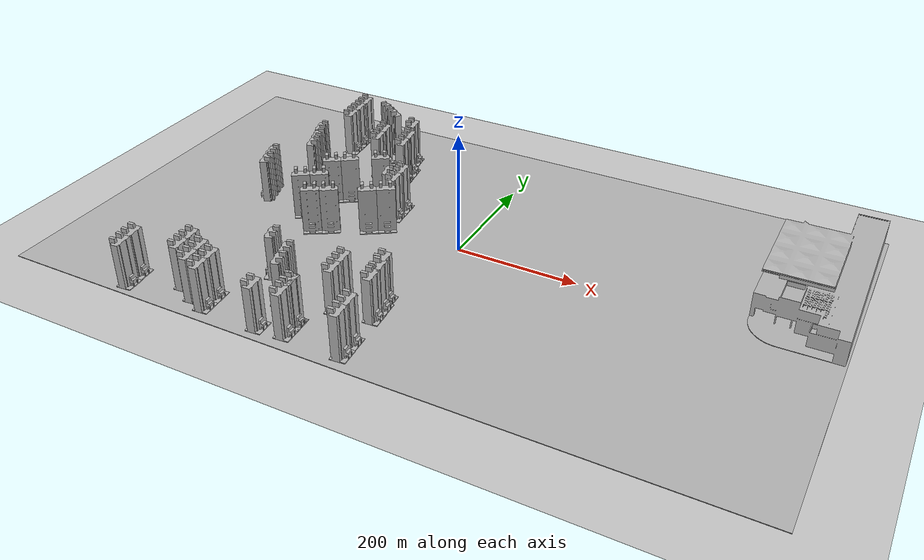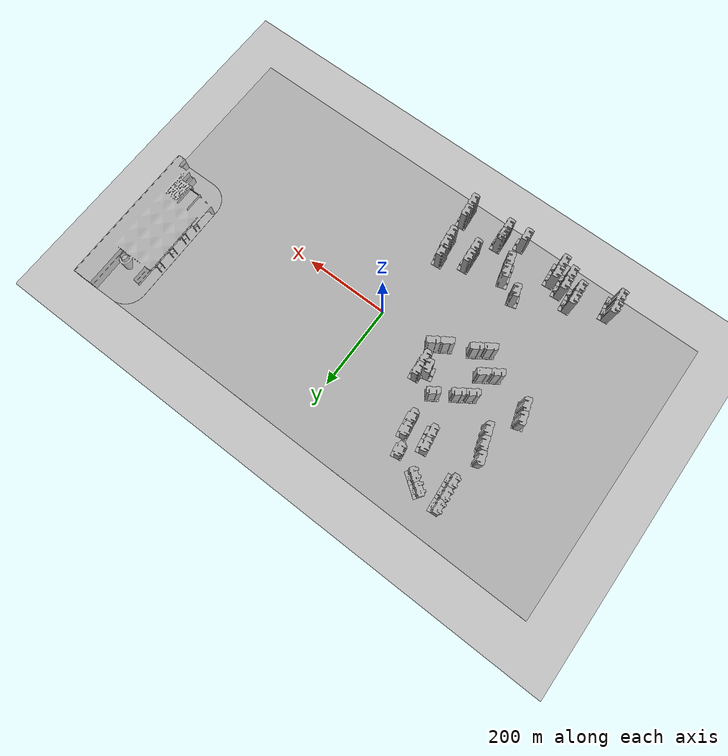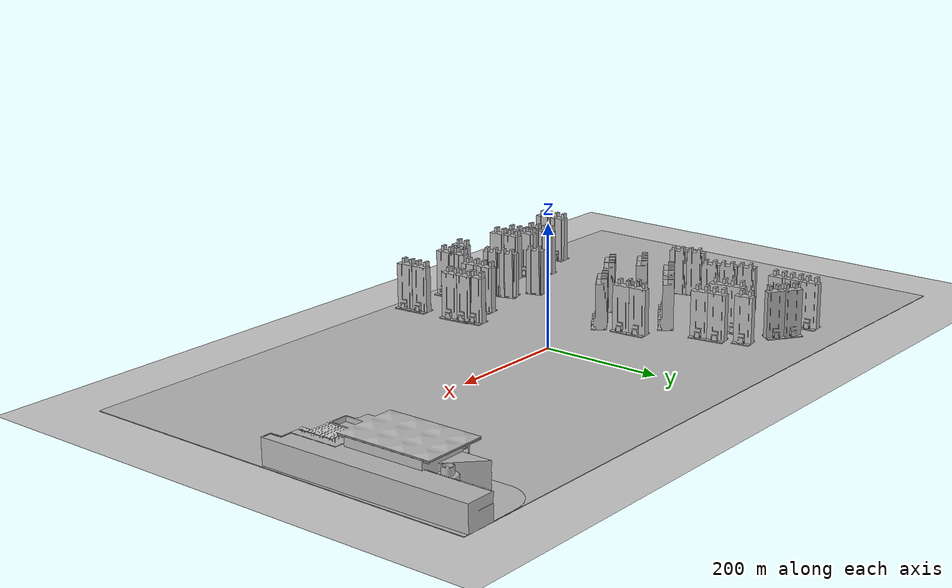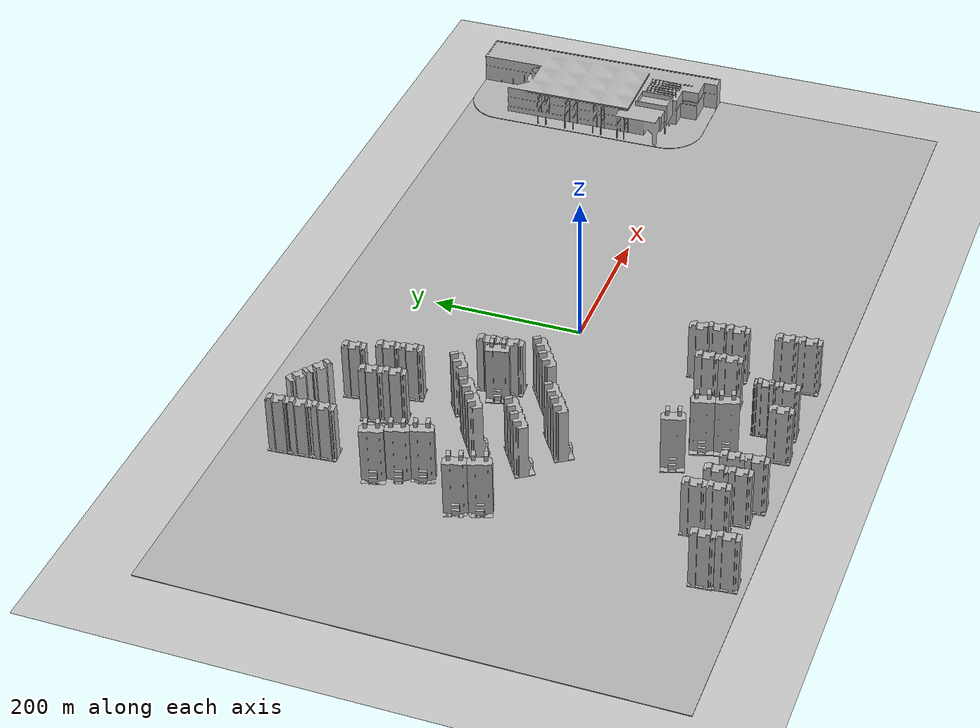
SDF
<sdf version="1.7">
 <world name="default">
  <light name="sun" type="directional">
   <pose>0 0 10 0 -0 0</pose>
   <diffuse>0.8 0.8 0.8 1</diffuse>
   <specular>0.2 0.2 0.2 1</specular>
   <attenuation>
    <range>1000</range>
    <constant>0.9</constant>
    <linear>0.01</linear>
    <quadratic>0.001</quadratic>
   </attenuation>
   <direction>-0.5 0.1 -0.9</direction>
   <spot><inner_angle>0</inner_angle><outer_angle>0</outer_angle><falloff>0</falloff></spot>
  </light>
  <model name="ground_plane">
   <static>1</static>
   <link name="link">
    <collision name="collision">
     <geometry><plane><normal>0 0 1</normal><size>1200 675</size></plane></geometry>
     <surface><friction><ode><mu>100</mu><mu2>50</mu2></ode></friction></surface>
    </collision>
    <visual name="visual">
     <cast_shadows>0</cast_shadows>
     <geometry><plane><normal>0 0 1</normal><size>1200 675</size></plane></geometry>
     <material>
      <script><uri>file://media/materials/scripts/gazebo.material</uri><name>Gazebo/Grey</name></script>
     </material>
    </visual>
   </link>
  </model>
  <gravity>0 0 -9.8</gravity>
  <magnetic_field>6e-06 2.3e-05 -4.2e-05</magnetic_field>
  <atmosphere type="adiabatic"/>
  <physics type="ode">
   <max_step_size>0.001</max_step_size>
   <real_time_factor>1</real_time_factor>
   <real_time_update_rate>1000</real_time_update_rate>
  </physics>
  <scene><ambient>0.4 0.4 0.4 1</ambient><background>0.7 0.7 0.7 1</background><shadows>1</shadows></scene>
  <spherical_coordinates>
   <surface_model>EARTH_WGS84</surface_model>
   <latitude_deg>0</latitude_deg>
   <longitude_deg>0</longitude_deg>
   <elevation>0</elevation>
   <heading_deg>0</heading_deg>
  </spherical_coordinates>
  <model name="plane">
   <static>1</static>
   <link name="link_0">
    <inertial>
     <mass>1</mass>
     <inertia>
      <ixx>0.166667</ixx>
      <ixy>0</ixy>
      <ixz>0</ixz>
      <iyy>0.166667</iyy>
      <iyz>0</iyz>
      <izz>0.166667</izz>
     </inertia>
    </inertial>
    <pose>-1.2e-05 0 0 0 -0 0</pose>
    <visual name="visual">
     <geometry>
      <mesh><uri>/home/leejeonghun/model_editor_models/plane/scripts/plane.dae</uri><scale>1 1 1</scale></mesh>
     </geometry>
     <material>
      <lighting>1</lighting>
      <script>
       <uri>/home/leejeonghun/model_editor_models/plane/scripts/plane.jpg</uri>
       <name>__default__</name>
      </script>
      <shader type="pixel"/>
     </material>
    </visual>
    <collision name="collision">
     <geometry>
      <mesh><uri>/home/leejeonghun/model_editor_models/plane/scripts/plane.dae</uri><scale>1 1 1</scale></mesh>
     </geometry>
     <surface>
      <friction>
       <ode><mu>1</mu><mu2>1</mu2><fdir1>0 0 0</fdir1><slip1>0</slip1><slip2>0</slip2></ode>
       <torsional>
        <coefficient>1</coefficient>
        <patch_radius>0</patch_radius>
        <surface_radius>0</surface_radius>
        <use_patch_radius>1</use_patch_radius>
        <ode><slip>0</slip></ode>
       </torsional>
      </friction>
      <bounce><restitution_coefficient>0</restitution_coefficient><threshold>1e+06</threshold></bounce>
      <contact>
       <collide_without_contact>0</collide_without_contact>
       <collide_without_contact_bitmask>1</collide_without_contact_bitmask>
       <collide_bitmask>1</collide_bitmask>
       <ode>
        <soft_cfm>0</soft_cfm>
        <soft_erp>0.2</soft_erp>
        <kp>1e+13</kp>
        <kd>1</kd>
        <max_vel>0.01</max_vel>
        <min_depth>0</min_depth>
       </ode>
       <bullet>
        <split_impulse>1</split_impulse>
        <split_impulse_penetration_threshold>-0.01</split_impulse_penetration_threshold>
        <soft_cfm>0</soft_cfm>
        <soft_erp>0.2</soft_erp>
        <kp>1e+13</kp>
        <kd>1</kd>
       </bullet>
      </contact>
     </surface>
    </collision>
   </link>
   <static>0</static>
   <pose>-1.96292 -0.549666 0 0 -0 0</pose>
  </model>
  <model name="airport">
   <static>1</static>
   <link name="link_0">
    <inertial>
     <mass>1</mass>
     <inertia>
      <ixx>0.166667</ixx>
      <ixy>0</ixy>
      <ixz>0</ixz>
      <iyy>0.166667</iyy>
      <iyz>0</iyz>
      <izz>0.166667</izz>
     </inertia>
    </inertial>
    <pose>4e-06 1e-06 0 0 -0 1.58504</pose>
    <visual name="visual">
     <geometry>
      <mesh>
       <uri>/home/leejeonghun/model_editor_models/airport/scripts/airport.dae</uri>
       <scale>0.6 0.6 0.8</scale>
      </mesh>
     </geometry>
     <material>
      <lighting>1</lighting>
      <script>
       <uri>/home/leejeonghun/model_editor_models/airport/scripts/airporrt.jpg</uri>
       <name>__default__</name>
      </script>
      <shader type="pixel"><normal_map>__default__</normal_map></shader>
     </material>
    </visual>
    <collision name="collision">
     <geometry>
      <mesh>
       <uri>/home/leejeonghun/model_editor_models/airport/scripts/airport.dae</uri>
       <scale>0.6 0.6 0.8</scale>
      </mesh>
     </geometry>
     <surface>
      <friction>
       <ode><mu>1</mu><mu2>1</mu2><fdir1>0 0 0</fdir1><slip1>0</slip1><slip2>0</slip2></ode>
       <torsional>
        <coefficient>1</coefficient>
        <patch_radius>0</patch_radius>
        <surface_radius>0</surface_radius>
        <use_patch_radius>1</use_patch_radius>
        <ode><slip>0</slip></ode>
       </torsional>
      </friction>
      <bounce><restitution_coefficient>0</restitution_coefficient><threshold>1e+06</threshold></bounce>
      <contact>
       <collide_without_contact>0</collide_without_contact>
       <collide_without_contact_bitmask>1</collide_without_contact_bitmask>
       <collide_bitmask>1</collide_bitmask>
       <ode>
        <soft_cfm>0</soft_cfm>
        <soft_erp>0.2</soft_erp>
        <kp>1e+13</kp>
        <kd>1</kd>
        <max_vel>0.01</max_vel>
        <min_depth>0</min_depth>
       </ode>
       <bullet>
        <split_impulse>1</split_impulse>
        <split_impulse_penetration_threshold>-0.01</split_impulse_penetration_threshold>
        <soft_cfm>0</soft_cfm>
        <soft_erp>0.2</soft_erp>
        <kp>1e+13</kp>
        <kd>1</kd>
       </bullet>
      </contact>
     </surface>
    </collision>
   </link>
   <static>0</static>
   <pose>500.172 162.388 0.746826 0 -0 3.13851</pose>
  </model>
  <model name="apartment">
   <static>1</static>
   <link name="link_0">
    <inertial>
     <mass>1</mass>
     <inertia>
      <ixx>0.166667</ixx>
      <ixy>0</ixy>
      <ixz>0</ixz>
      <iyy>0.166667</iyy>
      <iyz>0</iyz>
      <izz>0.166667</izz>
     </inertia>
    </inertial>
    <pose>0.000226 2e-06 0 0 -0 0</pose>
    <visual name="visual">
     <geometry>
      <mesh>
       <uri>/home/leejeonghun/model_editor_models/apartment/scripts/apartment.dae</uri>
       <scale>0.4 0.4 0.5</scale>
      </mesh>
     </geometry>
     <material>
      <lighting>1</lighting>
      <script>
       <uri>/home/leejeonghun/model_editor_models/apartment/scripts/building.jpg</uri>
       <name>__default__</name>
      </script>
      <shader type="pixel"/>
     </material>
    </visual>
    <collision name="collision">
     <geometry>
      <mesh>
       <uri>/home/leejeonghun/model_editor_models/apartment/scripts/apartment.dae</uri>
       <scale>0.4 0.4 0.5</scale>
      </mesh>
     </geometry>
     <surface>
      <friction>
       <ode><mu>1</mu><mu2>1</mu2><fdir1>0 0 0</fdir1><slip1>0</slip1><slip2>0</slip2></ode>
       <torsional>
        <coefficient>1</coefficient>
        <patch_radius>0</patch_radius>
        <surface_radius>0</surface_radius>
        <use_patch_radius>1</use_patch_radius>
        <ode><slip>0</slip></ode>
       </torsional>
      </friction>
      <bounce><restitution_coefficient>0</restitution_coefficient><threshold>1e+06</threshold></bounce>
      <contact>
       <collide_without_contact>0</collide_without_contact>
       <collide_without_contact_bitmask>1</collide_without_contact_bitmask>
       <collide_bitmask>1</collide_bitmask>
       <ode>
        <soft_cfm>0</soft_cfm>
        <soft_erp>0.2</soft_erp>
        <kp>1e+13</kp>
        <kd>1</kd>
        <max_vel>0.01</max_vel>
        <min_depth>0</min_depth>
       </ode>
       <bullet>
        <split_impulse>1</split_impulse>
        <split_impulse_penetration_threshold>-0.01</split_impulse_penetration_threshold>
        <soft_cfm>0</soft_cfm>
        <soft_erp>0.2</soft_erp>
        <kp>1e+13</kp>
        <kd>1</kd>
       </bullet>
      </contact>
     </surface>
    </collision>
   </link>
   <static>0</static>
   <pose>-157.514 -14.5633 1.45895 0 -0 0.586882</pose>
  </model>
  <model name="apartment_clone">
   <static>1</static>
   <link name="link_0">
    <inertial>
     <mass>1</mass>
     <inertia>
      <ixx>0.166667</ixx>
      <ixy>0</ixy>
      <ixz>0</ixz>
      <iyy>0.166667</iyy>
      <iyz>0</iyz>
      <izz>0.166667</izz>
     </inertia>
    </inertial>
    <pose>0.000226 2e-06 0 0 -0 0</pose>
    <visual name="visual">
     <geometry>
      <mesh>
       <uri>/home/leejeonghun/model_editor_models/apartment/scripts/apartment.dae</uri>
       <scale>0.4 0.4 0.5</scale>
      </mesh>
     </geometry>
     <material>
      <lighting>1</lighting>
      <script>
       <uri>/home/leejeonghun/model_editor_models/apartment/scripts/building.jpg</uri>
       <name>__default__</name>
      </script>
      <shader type="pixel"/>
     </material>
    </visual>
    <collision name="collision">
     <geometry>
      <mesh>
       <uri>/home/leejeonghun/model_editor_models/apartment/scripts/apartment.dae</uri>
       <scale>0.4 0.4 0.5</scale>
      </mesh>
     </geometry>
     <surface>
      <friction>
       <ode><mu>1</mu><mu2>1</mu2><fdir1>0 0 0</fdir1><slip1>0</slip1><slip2>0</slip2></ode>
       <torsional>
        <coefficient>1</coefficient>
        <patch_radius>0</patch_radius>
        <surface_radius>0</surface_radius>
        <use_patch_radius>1</use_patch_radius>
        <ode><slip>0</slip></ode>
       </torsional>
      </friction>
      <bounce><restitution_coefficient>0</restitution_coefficient><threshold>1e+06</threshold></bounce>
      <contact>
       <collide_without_contact>0</collide_without_contact>
       <collide_without_contact_bitmask>1</collide_without_contact_bitmask>
       <collide_bitmask>1</collide_bitmask>
       <ode>
        <soft_cfm>0</soft_cfm>
        <soft_erp>0.2</soft_erp>
        <kp>1e+13</kp>
        <kd>1</kd>
        <max_vel>0.01</max_vel>
        <min_depth>0</min_depth>
       </ode>
       <bullet>
        <split_impulse>1</split_impulse>
        <split_impulse_penetration_threshold>-0.01</split_impulse_penetration_threshold>
        <soft_cfm>0</soft_cfm>
        <soft_erp>0.2</soft_erp>
        <kp>1e+13</kp>
        <kd>1</kd>
       </bullet>
      </contact>
     </surface>
    </collision>
   </link>
   <static>0</static>
   <pose>-132.523 1.79712 1.45895 0 -0 0.586882</pose>
  </model>
  <model name="apartment_clone_0">
   <static>1</static>
   <link name="link_0">
    <inertial>
     <mass>1</mass>
     <inertia>
      <ixx>0.166667</ixx>
      <ixy>0</ixy>
      <ixz>0</ixz>
      <iyy>0.166667</iyy>
      <iyz>0</iyz>
      <izz>0.166667</izz>
     </inertia>
    </inertial>
    <pose>0.000226 2e-06 0 0 -0 0</pose>
    <visual name="visual">
     <geometry>
      <mesh>
       <uri>/home/leejeonghun/model_editor_models/apartment/scripts/apartment.dae</uri>
       <scale>0.4 0.4 0.5</scale>
      </mesh>
     </geometry>
     <material>
      <lighting>1</lighting>
      <script>
       <uri>/home/leejeonghun/model_editor_models/apartment/scripts/building.jpg</uri>
       <name>__default__</name>
      </script>
      <shader type="pixel"/>
     </material>
    </visual>
    <collision name="collision">
     <geometry>
      <mesh>
       <uri>/home/leejeonghun/model_editor_models/apartment/scripts/apartment.dae</uri>
       <scale>0.4 0.4 0.5</scale>
      </mesh>
     </geometry>
     <surface>
      <friction>
       <ode><mu>1</mu><mu2>1</mu2><fdir1>0 0 0</fdir1><slip1>0</slip1><slip2>0</slip2></ode>
       <torsional>
        <coefficient>1</coefficient>
        <patch_radius>0</patch_radius>
        <surface_radius>0</surface_radius>
        <use_patch_radius>1</use_patch_radius>
        <ode><slip>0</slip></ode>
       </torsional>
      </friction>
      <bounce><restitution_coefficient>0</restitution_coefficient><threshold>1e+06</threshold></bounce>
      <contact>
       <collide_without_contact>0</collide_without_contact>
       <collide_without_contact_bitmask>1</collide_without_contact_bitmask>
       <collide_bitmask>1</collide_bitmask>
       <ode>
        <soft_cfm>0</soft_cfm>
        <soft_erp>0.2</soft_erp>
        <kp>1e+13</kp>
        <kd>1</kd>
        <max_vel>0.01</max_vel>
        <min_depth>0</min_depth>
       </ode>
       <bullet>
        <split_impulse>1</split_impulse>
        <split_impulse_penetration_threshold>-0.01</split_impulse_penetration_threshold>
        <soft_cfm>0</soft_cfm>
        <soft_erp>0.2</soft_erp>
        <kp>1e+13</kp>
        <kd>1</kd>
       </bullet>
      </contact>
     </surface>
    </collision>
   </link>
   <static>0</static>
   <pose>-237.455 -58.0506 2.31406 0 -0 0.561981</pose>
  </model>
  <model name="apartment_clone_2">
   <static>1</static>
   <link name="link_0">
    <inertial>
     <mass>1</mass>
     <inertia>
      <ixx>0.166667</ixx>
      <ixy>0</ixy>
      <ixz>0</ixz>
      <iyy>0.166667</iyy>
      <iyz>0</iyz>
      <izz>0.166667</izz>
     </inertia>
    </inertial>
    <pose>0.000226 2e-06 0 0 -0 0</pose>
    <visual name="visual">
     <geometry>
      <mesh>
       <uri>/home/leejeonghun/model_editor_models/apartment/scripts/apartment.dae</uri>
       <scale>0.4 0.4 0.5</scale>
      </mesh>
     </geometry>
     <material>
      <lighting>1</lighting>
      <script>
       <uri>/home/leejeonghun/model_editor_models/apartment/scripts/building.jpg</uri>
       <name>__default__</name>
      </script>
      <shader type="pixel"/>
     </material>
    </visual>
    <collision name="collision">
     <geometry>
      <mesh>
       <uri>/home/leejeonghun/model_editor_models/apartment/scripts/apartment.dae</uri>
       <scale>0.4 0.4 0.5</scale>
      </mesh>
     </geometry>
     <surface>
      <friction>
       <ode><mu>1</mu><mu2>1</mu2><fdir1>0 0 0</fdir1><slip1>0</slip1><slip2>0</slip2></ode>
       <torsional>
        <coefficient>1</coefficient>
        <patch_radius>0</patch_radius>
        <surface_radius>0</surface_radius>
        <use_patch_radius>1</use_patch_radius>
        <ode><slip>0</slip></ode>
       </torsional>
      </friction>
      <bounce><restitution_coefficient>0</restitution_coefficient><threshold>1e+06</threshold></bounce>
      <contact>
       <collide_without_contact>0</collide_without_contact>
       <collide_without_contact_bitmask>1</collide_without_contact_bitmask>
       <collide_bitmask>1</collide_bitmask>
       <ode>
        <soft_cfm>0</soft_cfm>
        <soft_erp>0.2</soft_erp>
        <kp>1e+13</kp>
        <kd>1</kd>
        <max_vel>0.01</max_vel>
        <min_depth>0</min_depth>
       </ode>
       <bullet>
        <split_impulse>1</split_impulse>
        <split_impulse_penetration_threshold>-0.01</split_impulse_penetration_threshold>
        <soft_cfm>0</soft_cfm>
        <soft_erp>0.2</soft_erp>
        <kp>1e+13</kp>
        <kd>1</kd>
       </bullet>
      </contact>
     </surface>
    </collision>
   </link>
   <static>0</static>
   <pose>-212.841 -41.619 1.45895 0 -0 0.586882</pose>
  </model>
  <model name="apartment_clone_3">
   <static>1</static>
   <link name="link_0">
    <inertial>
     <mass>1</mass>
     <inertia>
      <ixx>0.166667</ixx>
      <ixy>0</ixy>
      <ixz>0</ixz>
      <iyy>0.166667</iyy>
      <iyz>0</iyz>
      <izz>0.166667</izz>
     </inertia>
    </inertial>
    <pose>0.000226 2e-06 0 0 -0 0</pose>
    <visual name="visual">
     <geometry>
      <mesh>
       <uri>/home/leejeonghun/model_editor_models/apartment/scripts/apartment.dae</uri>
       <scale>0.4 0.4 0.5</scale>
      </mesh>
     </geometry>
     <material>
      <lighting>1</lighting>
      <script>
       <uri>/home/leejeonghun/model_editor_models/apartment/scripts/building.jpg</uri>
       <name>__default__</name>
      </script>
      <shader type="pixel"/>
     </material>
    </visual>
    <collision name="collision">
     <geometry>
      <mesh>
       <uri>/home/leejeonghun/model_editor_models/apartment/scripts/apartment.dae</uri>
       <scale>0.4 0.4 0.5</scale>
      </mesh>
     </geometry>
     <surface>
      <friction>
       <ode><mu>1</mu><mu2>1</mu2><fdir1>0 0 0</fdir1><slip1>0</slip1><slip2>0</slip2></ode>
       <torsional>
        <coefficient>1</coefficient>
        <patch_radius>0</patch_radius>
        <surface_radius>0</surface_radius>
        <use_patch_radius>1</use_patch_radius>
        <ode><slip>0</slip></ode>
       </torsional>
      </friction>
      <bounce><restitution_coefficient>0</restitution_coefficient><threshold>1e+06</threshold></bounce>
      <contact>
       <collide_without_contact>0</collide_without_contact>
       <collide_without_contact_bitmask>1</collide_without_contact_bitmask>
       <collide_bitmask>1</collide_bitmask>
       <ode>
        <soft_cfm>0</soft_cfm>
        <soft_erp>0.2</soft_erp>
        <kp>1e+13</kp>
        <kd>1</kd>
        <max_vel>0.01</max_vel>
        <min_depth>0</min_depth>
       </ode>
       <bullet>
        <split_impulse>1</split_impulse>
        <split_impulse_penetration_threshold>-0.01</split_impulse_penetration_threshold>
        <soft_cfm>0</soft_cfm>
        <soft_erp>0.2</soft_erp>
        <kp>1e+13</kp>
        <kd>1</kd>
       </bullet>
      </contact>
     </surface>
    </collision>
   </link>
   <static>0</static>
   <pose>-195.289 87.5395 1.45895 0 -0 0.586882</pose>
  </model>
  <model name="apartment_clone_4">
   <static>1</static>
   <link name="link_0">
    <inertial>
     <mass>1</mass>
     <inertia>
      <ixx>0.166667</ixx>
      <ixy>0</ixy>
      <ixz>0</ixz>
      <iyy>0.166667</iyy>
      <iyz>0</iyz>
      <izz>0.166667</izz>
     </inertia>
    </inertial>
    <pose>0.000226 2e-06 0 0 -0 0</pose>
    <visual name="visual">
     <geometry>
      <mesh>
       <uri>/home/leejeonghun/model_editor_models/apartment/scripts/apartment.dae</uri>
       <scale>0.4 0.4 0.5</scale>
      </mesh>
     </geometry>
     <material>
      <lighting>1</lighting>
      <script>
       <uri>/home/leejeonghun/model_editor_models/apartment/scripts/building.jpg</uri>
       <name>__default__</name>
      </script>
      <shader type="pixel"/>
     </material>
    </visual>
    <collision name="collision">
     <geometry>
      <mesh>
       <uri>/home/leejeonghun/model_editor_models/apartment/scripts/apartment.dae</uri>
       <scale>0.4 0.4 0.5</scale>
      </mesh>
     </geometry>
     <surface>
      <friction>
       <ode><mu>1</mu><mu2>1</mu2><fdir1>0 0 0</fdir1><slip1>0</slip1><slip2>0</slip2></ode>
       <torsional>
        <coefficient>1</coefficient>
        <patch_radius>0</patch_radius>
        <surface_radius>0</surface_radius>
        <use_patch_radius>1</use_patch_radius>
        <ode><slip>0</slip></ode>
       </torsional>
      </friction>
      <bounce><restitution_coefficient>0</restitution_coefficient><threshold>1e+06</threshold></bounce>
      <contact>
       <collide_without_contact>0</collide_without_contact>
       <collide_without_contact_bitmask>1</collide_without_contact_bitmask>
       <collide_bitmask>1</collide_bitmask>
       <ode>
        <soft_cfm>0</soft_cfm>
        <soft_erp>0.2</soft_erp>
        <kp>1e+13</kp>
        <kd>1</kd>
        <max_vel>0.01</max_vel>
        <min_depth>0</min_depth>
       </ode>
       <bullet>
        <split_impulse>1</split_impulse>
        <split_impulse_penetration_threshold>-0.01</split_impulse_penetration_threshold>
        <soft_cfm>0</soft_cfm>
        <soft_erp>0.2</soft_erp>
        <kp>1e+13</kp>
        <kd>1</kd>
       </bullet>
      </contact>
     </surface>
    </collision>
   </link>
   <static>0</static>
   <pose>-237.879 58.8763 1.45895 0 -0 0.586882</pose>
  </model>
  <model name="apartment_clone_5">
   <static>1</static>
   <link name="link_0">
    <inertial>
     <mass>1</mass>
     <inertia>
      <ixx>0.166667</ixx>
      <ixy>0</ixy>
      <ixz>0</ixz>
      <iyy>0.166667</iyy>
      <iyz>0</iyz>
      <izz>0.166667</izz>
     </inertia>
    </inertial>
    <pose>0.000226 2e-06 0 0 -0 0</pose>
    <visual name="visual">
     <geometry>
      <mesh>
       <uri>/home/leejeonghun/model_editor_models/apartment/scripts/apartment.dae</uri>
       <scale>0.4 0.4 0.5</scale>
      </mesh>
     </geometry>
     <material>
      <lighting>1</lighting>
      <script>
       <uri>/home/leejeonghun/model_editor_models/apartment/scripts/building.jpg</uri>
       <name>__default__</name>
      </script>
      <shader type="pixel"/>
     </material>
    </visual>
    <collision name="collision">
     <geometry>
      <mesh>
       <uri>/home/leejeonghun/model_editor_models/apartment/scripts/apartment.dae</uri>
       <scale>0.4 0.4 0.5</scale>
      </mesh>
     </geometry>
     <surface>
      <friction>
       <ode><mu>1</mu><mu2>1</mu2><fdir1>0 0 0</fdir1><slip1>0</slip1><slip2>0</slip2></ode>
       <torsional>
        <coefficient>1</coefficient>
        <patch_radius>0</patch_radius>
        <surface_radius>0</surface_radius>
        <use_patch_radius>1</use_patch_radius>
        <ode><slip>0</slip></ode>
       </torsional>
      </friction>
      <bounce><restitution_coefficient>0</restitution_coefficient><threshold>1e+06</threshold></bounce>
      <contact>
       <collide_without_contact>0</collide_without_contact>
       <collide_without_contact_bitmask>1</collide_without_contact_bitmask>
       <collide_bitmask>1</collide_bitmask>
       <ode>
        <soft_cfm>0</soft_cfm>
        <soft_erp>0.2</soft_erp>
        <kp>1e+13</kp>
        <kd>1</kd>
        <max_vel>0.01</max_vel>
        <min_depth>0</min_depth>
       </ode>
       <bullet>
        <split_impulse>1</split_impulse>
        <split_impulse_penetration_threshold>-0.01</split_impulse_penetration_threshold>
        <soft_cfm>0</soft_cfm>
        <soft_erp>0.2</soft_erp>
        <kp>1e+13</kp>
        <kd>1</kd>
       </bullet>
      </contact>
     </surface>
    </collision>
   </link>
   <static>0</static>
   <pose>-262.551 42.3093 1.45895 0 -0 0.586882</pose>
  </model>
  <model name="apartment_clone_6">
   <static>1</static>
   <link name="link_0">
    <inertial>
     <mass>1</mass>
     <inertia>
      <ixx>0.166667</ixx>
      <ixy>0</ixy>
      <ixz>0</ixz>
      <iyy>0.166667</iyy>
      <iyz>0</iyz>
      <izz>0.166667</izz>
     </inertia>
    </inertial>
    <pose>0.000226 2e-06 0 0 -0 0</pose>
    <visual name="visual">
     <geometry>
      <mesh>
       <uri>/home/leejeonghun/model_editor_models/apartment/scripts/apartment.dae</uri>
       <scale>0.4 0.4 0.5</scale>
      </mesh>
     </geometry>
     <material>
      <lighting>1</lighting>
      <script>
       <uri>/home/leejeonghun/model_editor_models/apartment/scripts/building.jpg</uri>
       <name>__default__</name>
      </script>
      <shader type="pixel"/>
     </material>
    </visual>
    <collision name="collision">
     <geometry>
      <mesh>
       <uri>/home/leejeonghun/model_editor_models/apartment/scripts/apartment.dae</uri>
       <scale>0.4 0.4 0.5</scale>
      </mesh>
     </geometry>
     <surface>
      <friction>
       <ode><mu>1</mu><mu2>1</mu2><fdir1>0 0 0</fdir1><slip1>0</slip1><slip2>0</slip2></ode>
       <torsional>
        <coefficient>1</coefficient>
        <patch_radius>0</patch_radius>
        <surface_radius>0</surface_radius>
        <use_patch_radius>1</use_patch_radius>
        <ode><slip>0</slip></ode>
       </torsional>
      </friction>
      <bounce><restitution_coefficient>0</restitution_coefficient><threshold>1e+06</threshold></bounce>
      <contact>
       <collide_without_contact>0</collide_without_contact>
       <collide_without_contact_bitmask>1</collide_without_contact_bitmask>
       <collide_bitmask>1</collide_bitmask>
       <ode>
        <soft_cfm>0</soft_cfm>
        <soft_erp>0.2</soft_erp>
        <kp>1e+13</kp>
        <kd>1</kd>
        <max_vel>0.01</max_vel>
        <min_depth>0</min_depth>
       </ode>
       <bullet>
        <split_impulse>1</split_impulse>
        <split_impulse_penetration_threshold>-0.01</split_impulse_penetration_threshold>
        <soft_cfm>0</soft_cfm>
        <soft_erp>0.2</soft_erp>
        <kp>1e+13</kp>
        <kd>1</kd>
       </bullet>
      </contact>
     </surface>
    </collision>
   </link>
   <static>0</static>
   <pose>-279.756 -22.2909 1.45895 0 -0 0.586882</pose>
  </model>
  <model name="apartment_clone_7">
   <static>1</static>
   <link name="link_0">
    <inertial>
     <mass>1</mass>
     <inertia>
      <ixx>0.166667</ixx>
      <ixy>0</ixy>
      <ixz>0</ixz>
      <iyy>0.166667</iyy>
      <iyz>0</iyz>
      <izz>0.166667</izz>
     </inertia>
    </inertial>
    <pose>0.000226 2e-06 0 0 -0 0</pose>
    <visual name="visual">
     <geometry>
      <mesh>
       <uri>/home/leejeonghun/model_editor_models/apartment/scripts/apartment.dae</uri>
       <scale>0.4 0.4 0.5</scale>
      </mesh>
     </geometry>
     <material>
      <lighting>1</lighting>
      <script>
       <uri>/home/leejeonghun/model_editor_models/apartment/scripts/building.jpg</uri>
       <name>__default__</name>
      </script>
      <shader type="pixel"/>
     </material>
    </visual>
    <collision name="collision">
     <geometry>
      <mesh>
       <uri>/home/leejeonghun/model_editor_models/apartment/scripts/apartment.dae</uri>
       <scale>0.4 0.4 0.5</scale>
      </mesh>
     </geometry>
     <surface>
      <friction>
       <ode><mu>1</mu><mu2>1</mu2><fdir1>0 0 0</fdir1><slip1>0</slip1><slip2>0</slip2></ode>
       <torsional>
        <coefficient>1</coefficient>
        <patch_radius>0</patch_radius>
        <surface_radius>0</surface_radius>
        <use_patch_radius>1</use_patch_radius>
        <ode><slip>0</slip></ode>
       </torsional>
      </friction>
      <bounce><restitution_coefficient>0</restitution_coefficient><threshold>1e+06</threshold></bounce>
      <contact>
       <collide_without_contact>0</collide_without_contact>
       <collide_without_contact_bitmask>1</collide_without_contact_bitmask>
       <collide_bitmask>1</collide_bitmask>
       <ode>
        <soft_cfm>0</soft_cfm>
        <soft_erp>0.2</soft_erp>
        <kp>1e+13</kp>
        <kd>1</kd>
        <max_vel>0.01</max_vel>
        <min_depth>0</min_depth>
       </ode>
       <bullet>
        <split_impulse>1</split_impulse>
        <split_impulse_penetration_threshold>-0.01</split_impulse_penetration_threshold>
        <soft_cfm>0</soft_cfm>
        <soft_erp>0.2</soft_erp>
        <kp>1e+13</kp>
        <kd>1</kd>
       </bullet>
      </contact>
     </surface>
    </collision>
   </link>
   <static>0</static>
   <pose>-254.849 -5.7921 1.45895 0 -0 0.586882</pose>
  </model>
  <model name="apartment_clone_8">
   <static>1</static>
   <link name="link_0">
    <inertial>
     <mass>1</mass>
     <inertia>
      <ixx>0.166667</ixx>
      <ixy>0</ixy>
      <ixz>0</ixz>
      <iyy>0.166667</iyy>
      <iyz>0</iyz>
      <izz>0.166667</izz>
     </inertia>
    </inertial>
    <pose>0.000226 2e-06 0 0 -0 0</pose>
    <visual name="visual">
     <geometry>
      <mesh>
       <uri>/home/leejeonghun/model_editor_models/apartment/scripts/apartment.dae</uri>
       <scale>0.4 0.4 0.5</scale>
      </mesh>
     </geometry>
     <material>
      <lighting>1</lighting>
      <script>
       <uri>/home/leejeonghun/model_editor_models/apartment/scripts/building.jpg</uri>
       <name>__default__</name>
      </script>
      <shader type="pixel"/>
     </material>
    </visual>
    <collision name="collision">
     <geometry>
      <mesh>
       <uri>/home/leejeonghun/model_editor_models/apartment/scripts/apartment.dae</uri>
       <scale>0.4 0.4 0.5</scale>
      </mesh>
     </geometry>
     <surface>
      <friction>
       <ode><mu>1</mu><mu2>1</mu2><fdir1>0 0 0</fdir1><slip1>0</slip1><slip2>0</slip2></ode>
       <torsional>
        <coefficient>1</coefficient>
        <patch_radius>0</patch_radius>
        <surface_radius>0</surface_radius>
        <use_patch_radius>1</use_patch_radius>
        <ode><slip>0</slip></ode>
       </torsional>
      </friction>
      <bounce><restitution_coefficient>0</restitution_coefficient><threshold>1e+06</threshold></bounce>
      <contact>
       <collide_without_contact>0</collide_without_contact>
       <collide_without_contact_bitmask>1</collide_without_contact_bitmask>
       <collide_bitmask>1</collide_bitmask>
       <ode>
        <soft_cfm>0</soft_cfm>
        <soft_erp>0.2</soft_erp>
        <kp>1e+13</kp>
        <kd>1</kd>
        <max_vel>0.01</max_vel>
        <min_depth>0</min_depth>
       </ode>
       <bullet>
        <split_impulse>1</split_impulse>
        <split_impulse_penetration_threshold>-0.01</split_impulse_penetration_threshold>
        <soft_cfm>0</soft_cfm>
        <soft_erp>0.2</soft_erp>
        <kp>1e+13</kp>
        <kd>1</kd>
       </bullet>
      </contact>
     </surface>
    </collision>
   </link>
   <static>0</static>
   <pose>-139.6 40.295 1.45895 0 -0 1.65687</pose>
  </model>
  <model name="apartment_clone_8_clone">
   <static>1</static>
   <link name="link_0">
    <inertial>
     <mass>1</mass>
     <inertia>
      <ixx>0.166667</ixx>
      <ixy>0</ixy>
      <ixz>0</ixz>
      <iyy>0.166667</iyy>
      <iyz>0</iyz>
      <izz>0.166667</izz>
     </inertia>
    </inertial>
    <pose>0.000226 2e-06 0 0 -0 0</pose>
    <visual name="visual">
     <geometry>
      <mesh>
       <uri>/home/leejeonghun/model_editor_models/apartment/scripts/apartment.dae</uri>
       <scale>0.4 0.4 0.5</scale>
      </mesh>
     </geometry>
     <material>
      <lighting>1</lighting>
      <script>
       <uri>/home/leejeonghun/model_editor_models/apartment/scripts/building.jpg</uri>
       <name>__default__</name>
      </script>
      <shader type="pixel"/>
     </material>
    </visual>
    <collision name="collision">
     <geometry>
      <mesh>
       <uri>/home/leejeonghun/model_editor_models/apartment/scripts/apartment.dae</uri>
       <scale>0.4 0.4 0.5</scale>
      </mesh>
     </geometry>
     <surface>
      <friction>
       <ode><mu>1</mu><mu2>1</mu2><fdir1>0 0 0</fdir1><slip1>0</slip1><slip2>0</slip2></ode>
       <torsional>
        <coefficient>1</coefficient>
        <patch_radius>0</patch_radius>
        <surface_radius>0</surface_radius>
        <use_patch_radius>1</use_patch_radius>
        <ode><slip>0</slip></ode>
       </torsional>
      </friction>
      <bounce><restitution_coefficient>0</restitution_coefficient><threshold>1e+06</threshold></bounce>
      <contact>
       <collide_without_contact>0</collide_without_contact>
       <collide_without_contact_bitmask>1</collide_without_contact_bitmask>
       <collide_bitmask>1</collide_bitmask>
       <ode>
        <soft_cfm>0</soft_cfm>
        <soft_erp>0.2</soft_erp>
        <kp>1e+13</kp>
        <kd>1</kd>
        <max_vel>0.01</max_vel>
        <min_depth>0</min_depth>
       </ode>
       <bullet>
        <split_impulse>1</split_impulse>
        <split_impulse_penetration_threshold>-0.01</split_impulse_penetration_threshold>
        <soft_cfm>0</soft_cfm>
        <soft_erp>0.2</soft_erp>
        <kp>1e+13</kp>
        <kd>1</kd>
       </bullet>
      </contact>
     </surface>
    </collision>
   </link>
   <static>0</static>
   <pose>-142.231 69.7113 1.45895 0 -0 1.65687</pose>
  </model>
  <model name="apartment_clone_8_clone_0">
   <static>1</static>
   <link name="link_0">
    <inertial>
     <mass>1</mass>
     <inertia>
      <ixx>0.166667</ixx>
      <ixy>0</ixy>
      <ixz>0</ixz>
      <iyy>0.166667</iyy>
      <iyz>0</iyz>
      <izz>0.166667</izz>
     </inertia>
    </inertial>
    <pose>0.000226 2e-06 0 0 -0 0</pose>
    <visual name="visual">
     <geometry>
      <mesh>
       <uri>/home/leejeonghun/model_editor_models/apartment/scripts/apartment.dae</uri>
       <scale>0.4 0.4 0.5</scale>
      </mesh>
     </geometry>
     <material>
      <lighting>1</lighting>
      <script>
       <uri>/home/leejeonghun/model_editor_models/apartment/scripts/building.jpg</uri>
       <name>__default__</name>
      </script>
      <shader type="pixel"/>
     </material>
    </visual>
    <collision name="collision">
     <geometry>
      <mesh>
       <uri>/home/leejeonghun/model_editor_models/apartment/scripts/apartment.dae</uri>
       <scale>0.4 0.4 0.5</scale>
      </mesh>
     </geometry>
     <surface>
      <friction>
       <ode><mu>1</mu><mu2>1</mu2><fdir1>0 0 0</fdir1><slip1>0</slip1><slip2>0</slip2></ode>
       <torsional>
        <coefficient>1</coefficient>
        <patch_radius>0</patch_radius>
        <surface_radius>0</surface_radius>
        <use_patch_radius>1</use_patch_radius>
        <ode><slip>0</slip></ode>
       </torsional>
      </friction>
      <bounce><restitution_coefficient>0</restitution_coefficient><threshold>1e+06</threshold></bounce>
      <contact>
       <collide_without_contact>0</collide_without_contact>
       <collide_without_contact_bitmask>1</collide_without_contact_bitmask>
       <collide_bitmask>1</collide_bitmask>
       <ode>
        <soft_cfm>0</soft_cfm>
        <soft_erp>0.2</soft_erp>
        <kp>1e+13</kp>
        <kd>1</kd>
        <max_vel>0.01</max_vel>
        <min_depth>0</min_depth>
       </ode>
       <bullet>
        <split_impulse>1</split_impulse>
        <split_impulse_penetration_threshold>-0.01</split_impulse_penetration_threshold>
        <soft_cfm>0</soft_cfm>
        <soft_erp>0.2</soft_erp>
        <kp>1e+13</kp>
        <kd>1</kd>
       </bullet>
      </contact>
     </surface>
    </collision>
   </link>
   <static>0</static>
   <pose>-336.315 267.967 1.45895 0 -0 1.65687</pose>
  </model>
  <model name="apartment_clone_8_clone_1">
   <static>1</static>
   <link name="link_0">
    <inertial>
     <mass>1</mass>
     <inertia>
      <ixx>0.166667</ixx>
      <ixy>0</ixy>
      <ixz>0</ixz>
      <iyy>0.166667</iyy>
      <iyz>0</iyz>
      <izz>0.166667</izz>
     </inertia>
    </inertial>
    <pose>0.000226 2e-06 0 0 -0 0</pose>
    <visual name="visual">
     <geometry>
      <mesh>
       <uri>/home/leejeonghun/model_editor_models/apartment/scripts/apartment.dae</uri>
       <scale>0.4 0.4 0.5</scale>
      </mesh>
     </geometry>
     <material>
      <lighting>1</lighting>
      <script>
       <uri>/home/leejeonghun/model_editor_models/apartment/scripts/building.jpg</uri>
       <name>__default__</name>
      </script>
      <shader type="pixel"/>
     </material>
    </visual>
    <collision name="collision">
     <geometry>
      <mesh>
       <uri>/home/leejeonghun/model_editor_models/apartment/scripts/apartment.dae</uri>
       <scale>0.4 0.4 0.5</scale>
      </mesh>
     </geometry>
     <surface>
      <friction>
       <ode><mu>1</mu><mu2>1</mu2><fdir1>0 0 0</fdir1><slip1>0</slip1><slip2>0</slip2></ode>
       <torsional>
        <coefficient>1</coefficient>
        <patch_radius>0</patch_radius>
        <surface_radius>0</surface_radius>
        <use_patch_radius>1</use_patch_radius>
        <ode><slip>0</slip></ode>
       </torsional>
      </friction>
      <bounce><restitution_coefficient>0</restitution_coefficient><threshold>1e+06</threshold></bounce>
      <contact>
       <collide_without_contact>0</collide_without_contact>
       <collide_without_contact_bitmask>1</collide_without_contact_bitmask>
       <collide_bitmask>1</collide_bitmask>
       <ode>
        <soft_cfm>0</soft_cfm>
        <soft_erp>0.2</soft_erp>
        <kp>1e+13</kp>
        <kd>1</kd>
        <max_vel>0.01</max_vel>
        <min_depth>0</min_depth>
       </ode>
       <bullet>
        <split_impulse>1</split_impulse>
        <split_impulse_penetration_threshold>-0.01</split_impulse_penetration_threshold>
        <soft_cfm>0</soft_cfm>
        <soft_erp>0.2</soft_erp>
        <kp>1e+13</kp>
        <kd>1</kd>
       </bullet>
      </contact>
     </surface>
    </collision>
   </link>
   <static>0</static>
   <pose>-334.105 239.915 1.45895 0 -0 1.65687</pose>
  </model>
  <model name="apartment_clone_8_clone_2">
   <static>1</static>
   <link name="link_0">
    <inertial>
     <mass>1</mass>
     <inertia>
      <ixx>0.166667</ixx>
      <ixy>0</ixy>
      <ixz>0</ixz>
      <iyy>0.166667</iyy>
      <iyz>0</iyz>
      <izz>0.166667</izz>
     </inertia>
    </inertial>
    <pose>0.000226 2e-06 0 0 -0 0</pose>
    <visual name="visual">
     <geometry>
      <mesh>
       <uri>/home/leejeonghun/model_editor_models/apartment/scripts/apartment.dae</uri>
       <scale>0.4 0.4 0.5</scale>
      </mesh>
     </geometry>
     <material>
      <lighting>1</lighting>
      <script>
       <uri>/home/leejeonghun/model_editor_models/apartment/scripts/building.jpg</uri>
       <name>__default__</name>
      </script>
      <shader type="pixel"/>
     </material>
    </visual>
    <collision name="collision">
     <geometry>
      <mesh>
       <uri>/home/leejeonghun/model_editor_models/apartment/scripts/apartment.dae</uri>
       <scale>0.4 0.4 0.5</scale>
      </mesh>
     </geometry>
     <surface>
      <friction>
       <ode><mu>1</mu><mu2>1</mu2><fdir1>0 0 0</fdir1><slip1>0</slip1><slip2>0</slip2></ode>
       <torsional>
        <coefficient>1</coefficient>
        <patch_radius>0</patch_radius>
        <surface_radius>0</surface_radius>
        <use_patch_radius>1</use_patch_radius>
        <ode><slip>0</slip></ode>
       </torsional>
      </friction>
      <bounce><restitution_coefficient>0</restitution_coefficient><threshold>1e+06</threshold></bounce>
      <contact>
       <collide_without_contact>0</collide_without_contact>
       <collide_without_contact_bitmask>1</collide_without_contact_bitmask>
       <collide_bitmask>1</collide_bitmask>
       <ode>
        <soft_cfm>0</soft_cfm>
        <soft_erp>0.2</soft_erp>
        <kp>1e+13</kp>
        <kd>1</kd>
        <max_vel>0.01</max_vel>
        <min_depth>0</min_depth>
       </ode>
       <bullet>
        <split_impulse>1</split_impulse>
        <split_impulse_penetration_threshold>-0.01</split_impulse_penetration_threshold>
        <soft_cfm>0</soft_cfm>
        <soft_erp>0.2</soft_erp>
        <kp>1e+13</kp>
        <kd>1</kd>
       </bullet>
      </contact>
     </surface>
    </collision>
   </link>
   <static>0</static>
   <pose>-331.53 210.597 1.45895 0 -0 1.65687</pose>
  </model>
  <model name="apartment_clone_8_clone_3">
   <static>1</static>
   <link name="link_0">
    <inertial>
     <mass>1</mass>
     <inertia>
      <ixx>0.166667</ixx>
      <ixy>0</ixy>
      <ixz>0</ixz>
      <iyy>0.166667</iyy>
      <iyz>0</iyz>
      <izz>0.166667</izz>
     </inertia>
    </inertial>
    <pose>0.000226 2e-06 0 0 -0 0</pose>
    <visual name="visual">
     <geometry>
      <mesh>
       <uri>/home/leejeonghun/model_editor_models/apartment/scripts/apartment.dae</uri>
       <scale>0.4 0.4 0.5</scale>
      </mesh>
     </geometry>
     <material>
      <lighting>1</lighting>
      <script>
       <uri>/home/leejeonghun/model_editor_models/apartment/scripts/building.jpg</uri>
       <name>__default__</name>
      </script>
      <shader type="pixel"/>
     </material>
    </visual>
    <collision name="collision">
     <geometry>
      <mesh>
       <uri>/home/leejeonghun/model_editor_models/apartment/scripts/apartment.dae</uri>
       <scale>0.4 0.4 0.5</scale>
      </mesh>
     </geometry>
     <surface>
      <friction>
       <ode><mu>1</mu><mu2>1</mu2><fdir1>0 0 0</fdir1><slip1>0</slip1><slip2>0</slip2></ode>
       <torsional>
        <coefficient>1</coefficient>
        <patch_radius>0</patch_radius>
        <surface_radius>0</surface_radius>
        <use_patch_radius>1</use_patch_radius>
        <ode><slip>0</slip></ode>
       </torsional>
      </friction>
      <bounce><restitution_coefficient>0</restitution_coefficient><threshold>1e+06</threshold></bounce>
      <contact>
       <collide_without_contact>0</collide_without_contact>
       <collide_without_contact_bitmask>1</collide_without_contact_bitmask>
       <collide_bitmask>1</collide_bitmask>
       <ode>
        <soft_cfm>0</soft_cfm>
        <soft_erp>0.2</soft_erp>
        <kp>1e+13</kp>
        <kd>1</kd>
        <max_vel>0.01</max_vel>
        <min_depth>0</min_depth>
       </ode>
       <bullet>
        <split_impulse>1</split_impulse>
        <split_impulse_penetration_threshold>-0.01</split_impulse_penetration_threshold>
        <soft_cfm>0</soft_cfm>
        <soft_erp>0.2</soft_erp>
        <kp>1e+13</kp>
        <kd>1</kd>
       </bullet>
      </contact>
     </surface>
    </collision>
   </link>
   <static>0</static>
   <pose>-285.637 263.644 1.45895 0 -0 2.51739</pose>
  </model>
  <model name="apartment_clone_8_clone_3_clone">
   <static>1</static>
   <link name="link_0">
    <inertial>
     <mass>1</mass>
     <inertia>
      <ixx>0.166667</ixx>
      <ixy>0</ixy>
      <ixz>0</ixz>
      <iyy>0.166667</iyy>
      <iyz>0</iyz>
      <izz>0.166667</izz>
     </inertia>
    </inertial>
    <pose>0.000226 2e-06 0 0 -0 0</pose>
    <visual name="visual">
     <geometry>
      <mesh>
       <uri>/home/leejeonghun/model_editor_models/apartment/scripts/apartment.dae</uri>
       <scale>0.4 0.4 0.5</scale>
      </mesh>
     </geometry>
     <material>
      <lighting>1</lighting>
      <script>
       <uri>/home/leejeonghun/model_editor_models/apartment/scripts/building.jpg</uri>
       <name>__default__</name>
      </script>
      <shader type="pixel"/>
     </material>
    </visual>
    <collision name="collision">
     <geometry>
      <mesh>
       <uri>/home/leejeonghun/model_editor_models/apartment/scripts/apartment.dae</uri>
       <scale>0.4 0.4 0.5</scale>
      </mesh>
     </geometry>
     <surface>
      <friction>
       <ode><mu>1</mu><mu2>1</mu2><fdir1>0 0 0</fdir1><slip1>0</slip1><slip2>0</slip2></ode>
       <torsional>
        <coefficient>1</coefficient>
        <patch_radius>0</patch_radius>
        <surface_radius>0</surface_radius>
        <use_patch_radius>1</use_patch_radius>
        <ode><slip>0</slip></ode>
       </torsional>
      </friction>
      <bounce><restitution_coefficient>0</restitution_coefficient><threshold>1e+06</threshold></bounce>
      <contact>
       <collide_without_contact>0</collide_without_contact>
       <collide_without_contact_bitmask>1</collide_without_contact_bitmask>
       <collide_bitmask>1</collide_bitmask>
       <ode>
        <soft_cfm>0</soft_cfm>
        <soft_erp>0.2</soft_erp>
        <kp>1e+13</kp>
        <kd>1</kd>
        <max_vel>0.01</max_vel>
        <min_depth>0</min_depth>
       </ode>
       <bullet>
        <split_impulse>1</split_impulse>
        <split_impulse_penetration_threshold>-0.01</split_impulse_penetration_threshold>
        <soft_cfm>0</soft_cfm>
        <soft_erp>0.2</soft_erp>
        <kp>1e+13</kp>
        <kd>1</kd>
       </bullet>
      </contact>
     </surface>
    </collision>
   </link>
   <static>0</static>
   <pose>-261.931 246.709 1.45895 0 -0 2.51739</pose>
  </model>
  <model name="apartment_clone_8_clone_3_clone_0">
   <static>1</static>
   <link name="link_0">
    <inertial>
     <mass>1</mass>
     <inertia>
      <ixx>0.166667</ixx>
      <ixy>0</ixy>
      <ixz>0</ixz>
      <iyy>0.166667</iyy>
      <iyz>0</iyz>
      <izz>0.166667</izz>
     </inertia>
    </inertial>
    <pose>0.000226 2e-06 0 0 -0 0</pose>
    <visual name="visual">
     <geometry>
      <mesh>
       <uri>/home/leejeonghun/model_editor_models/apartment/scripts/apartment.dae</uri>
       <scale>0.4 0.4 0.5</scale>
      </mesh>
     </geometry>
     <material>
      <lighting>1</lighting>
      <script>
       <uri>/home/leejeonghun/model_editor_models/apartment/scripts/building.jpg</uri>
       <name>__default__</name>
      </script>
      <shader type="pixel"/>
     </material>
    </visual>
    <collision name="collision">
     <geometry>
      <mesh>
       <uri>/home/leejeonghun/model_editor_models/apartment/scripts/apartment.dae</uri>
       <scale>0.4 0.4 0.5</scale>
      </mesh>
     </geometry>
     <surface>
      <friction>
       <ode><mu>1</mu><mu2>1</mu2><fdir1>0 0 0</fdir1><slip1>0</slip1><slip2>0</slip2></ode>
       <torsional>
        <coefficient>1</coefficient>
        <patch_radius>0</patch_radius>
        <surface_radius>0</surface_radius>
        <use_patch_radius>1</use_patch_radius>
        <ode><slip>0</slip></ode>
       </torsional>
      </friction>
      <bounce><restitution_coefficient>0</restitution_coefficient><threshold>1e+06</threshold></bounce>
      <contact>
       <collide_without_contact>0</collide_without_contact>
       <collide_without_contact_bitmask>1</collide_without_contact_bitmask>
       <collide_bitmask>1</collide_bitmask>
       <ode>
        <soft_cfm>0</soft_cfm>
        <soft_erp>0.2</soft_erp>
        <kp>1e+13</kp>
        <kd>1</kd>
        <max_vel>0.01</max_vel>
        <min_depth>0</min_depth>
       </ode>
       <bullet>
        <split_impulse>1</split_impulse>
        <split_impulse_penetration_threshold>-0.01</split_impulse_penetration_threshold>
        <soft_cfm>0</soft_cfm>
        <soft_erp>0.2</soft_erp>
        <kp>1e+13</kp>
        <kd>1</kd>
       </bullet>
      </contact>
     </surface>
    </collision>
   </link>
   <static>0</static>
   <pose>-245.732 185.285 1.45895 0 -0 1.72652</pose>
  </model>
  <model name="apartment_clone_8_clone_3_clone_0_clone">
   <static>1</static>
   <link name="link_0">
    <inertial>
     <mass>1</mass>
     <inertia>
      <ixx>0.166667</ixx>
      <ixy>0</ixy>
      <ixz>0</ixz>
      <iyy>0.166667</iyy>
      <iyz>0</iyz>
      <izz>0.166667</izz>
     </inertia>
    </inertial>
    <pose>0.000226 2e-06 0 0 -0 0</pose>
    <visual name="visual">
     <geometry>
      <mesh>
       <uri>/home/leejeonghun/model_editor_models/apartment/scripts/apartment.dae</uri>
       <scale>0.4 0.4 0.5</scale>
      </mesh>
     </geometry>
     <material>
      <lighting>1</lighting>
      <script>
       <uri>/home/leejeonghun/model_editor_models/apartment/scripts/building.jpg</uri>
       <name>__default__</name>
      </script>
      <shader type="pixel"/>
     </material>
    </visual>
    <collision name="collision">
     <geometry>
      <mesh>
       <uri>/home/leejeonghun/model_editor_models/apartment/scripts/apartment.dae</uri>
       <scale>0.4 0.4 0.5</scale>
      </mesh>
     </geometry>
     <surface>
      <friction>
       <ode><mu>1</mu><mu2>1</mu2><fdir1>0 0 0</fdir1><slip1>0</slip1><slip2>0</slip2></ode>
       <torsional>
        <coefficient>1</coefficient>
        <patch_radius>0</patch_radius>
        <surface_radius>0</surface_radius>
        <use_patch_radius>1</use_patch_radius>
        <ode><slip>0</slip></ode>
       </torsional>
      </friction>
      <bounce><restitution_coefficient>0</restitution_coefficient><threshold>1e+06</threshold></bounce>
      <contact>
       <collide_without_contact>0</collide_without_contact>
       <collide_without_contact_bitmask>1</collide_without_contact_bitmask>
       <collide_bitmask>1</collide_bitmask>
       <ode>
        <soft_cfm>0</soft_cfm>
        <soft_erp>0.2</soft_erp>
        <kp>1e+13</kp>
        <kd>1</kd>
        <max_vel>0.01</max_vel>
        <min_depth>0</min_depth>
       </ode>
       <bullet>
        <split_impulse>1</split_impulse>
        <split_impulse_penetration_threshold>-0.01</split_impulse_penetration_threshold>
        <soft_cfm>0</soft_cfm>
        <soft_erp>0.2</soft_erp>
        <kp>1e+13</kp>
        <kd>1</kd>
       </bullet>
      </contact>
     </surface>
    </collision>
   </link>
   <static>0</static>
   <pose>-240.976 156.074 1.45895 0 -0 1.72652</pose>
  </model>
  <model name="apartment_clone_8_clone_3_clone_0_clone_0">
   <static>1</static>
   <link name="link_0">
    <inertial>
     <mass>1</mass>
     <inertia>
      <ixx>0.166667</ixx>
      <ixy>0</ixy>
      <ixz>0</ixz>
      <iyy>0.166667</iyy>
      <iyz>0</iyz>
      <izz>0.166667</izz>
     </inertia>
    </inertial>
    <pose>0.000226 2e-06 0 0 -0 0</pose>
    <visual name="visual">
     <geometry>
      <mesh>
       <uri>/home/leejeonghun/model_editor_models/apartment/scripts/apartment.dae</uri>
       <scale>0.4 0.4 0.5</scale>
      </mesh>
     </geometry>
     <material>
      <lighting>1</lighting>
      <script>
       <uri>/home/leejeonghun/model_editor_models/apartment/scripts/building.jpg</uri>
       <name>__default__</name>
      </script>
      <shader type="pixel"/>
     </material>
    </visual>
    <collision name="collision">
     <geometry>
      <mesh>
       <uri>/home/leejeonghun/model_editor_models/apartment/scripts/apartment.dae</uri>
       <scale>0.4 0.4 0.5</scale>
      </mesh>
     </geometry>
     <surface>
      <friction>
       <ode><mu>1</mu><mu2>1</mu2><fdir1>0 0 0</fdir1><slip1>0</slip1><slip2>0</slip2></ode>
       <torsional>
        <coefficient>1</coefficient>
        <patch_radius>0</patch_radius>
        <surface_radius>0</surface_radius>
        <use_patch_radius>1</use_patch_radius>
        <ode><slip>0</slip></ode>
       </torsional>
      </friction>
      <bounce><restitution_coefficient>0</restitution_coefficient><threshold>1e+06</threshold></bounce>
      <contact>
       <collide_without_contact>0</collide_without_contact>
       <collide_without_contact_bitmask>1</collide_without_contact_bitmask>
       <collide_bitmask>1</collide_bitmask>
       <ode>
        <soft_cfm>0</soft_cfm>
        <soft_erp>0.2</soft_erp>
        <kp>1e+13</kp>
        <kd>1</kd>
        <max_vel>0.01</max_vel>
        <min_depth>0</min_depth>
       </ode>
       <bullet>
        <split_impulse>1</split_impulse>
        <split_impulse_penetration_threshold>-0.01</split_impulse_penetration_threshold>
        <soft_cfm>0</soft_cfm>
        <soft_erp>0.2</soft_erp>
        <kp>1e+13</kp>
        <kd>1</kd>
       </bullet>
      </contact>
     </surface>
    </collision>
   </link>
   <static>0</static>
   <pose>-190.441 154.89 1.45895 0 -0 1.72652</pose>
  </model>
  <model name="apartment_clone_8_clone_3_clone_0_clone_1">
   <static>1</static>
   <link name="link_0">
    <inertial>
     <mass>1</mass>
     <inertia>
      <ixx>0.166667</ixx>
      <ixy>0</ixy>
      <ixz>0</ixz>
      <iyy>0.166667</iyy>
      <iyz>0</iyz>
      <izz>0.166667</izz>
     </inertia>
    </inertial>
    <pose>0.000226 2e-06 0 0 -0 0</pose>
    <visual name="visual">
     <geometry>
      <mesh>
       <uri>/home/leejeonghun/model_editor_models/apartment/scripts/apartment.dae</uri>
       <scale>0.4 0.4 0.5</scale>
      </mesh>
     </geometry>
     <material>
      <lighting>1</lighting>
      <script>
       <uri>/home/leejeonghun/model_editor_models/apartment/scripts/building.jpg</uri>
       <name>__default__</name>
      </script>
      <shader type="pixel"/>
     </material>
    </visual>
    <collision name="collision">
     <geometry>
      <mesh>
       <uri>/home/leejeonghun/model_editor_models/apartment/scripts/apartment.dae</uri>
       <scale>0.4 0.4 0.5</scale>
      </mesh>
     </geometry>
     <surface>
      <friction>
       <ode><mu>1</mu><mu2>1</mu2><fdir1>0 0 0</fdir1><slip1>0</slip1><slip2>0</slip2></ode>
       <torsional>
        <coefficient>1</coefficient>
        <patch_radius>0</patch_radius>
        <surface_radius>0</surface_radius>
        <use_patch_radius>1</use_patch_radius>
        <ode><slip>0</slip></ode>
       </torsional>
      </friction>
      <bounce><restitution_coefficient>0</restitution_coefficient><threshold>1e+06</threshold></bounce>
      <contact>
       <collide_without_contact>0</collide_without_contact>
       <collide_without_contact_bitmask>1</collide_without_contact_bitmask>
       <collide_bitmask>1</collide_bitmask>
       <ode>
        <soft_cfm>0</soft_cfm>
        <soft_erp>0.2</soft_erp>
        <kp>1e+13</kp>
        <kd>1</kd>
        <max_vel>0.01</max_vel>
        <min_depth>0</min_depth>
       </ode>
       <bullet>
        <split_impulse>1</split_impulse>
        <split_impulse_penetration_threshold>-0.01</split_impulse_penetration_threshold>
        <soft_cfm>0</soft_cfm>
        <soft_erp>0.2</soft_erp>
        <kp>1e+13</kp>
        <kd>1</kd>
       </bullet>
      </contact>
     </surface>
    </collision>
   </link>
   <static>0</static>
   <pose>-194.757 183.695 1.45895 0 -0 1.72652</pose>
  </model>
  <model name="apartment_clone_8_clone_3_clone_0_clone_2">
   <static>1</static>
   <link name="link_0">
    <inertial>
     <mass>1</mass>
     <inertia>
      <ixx>0.166667</ixx>
      <ixy>0</ixy>
      <ixz>0</ixz>
      <iyy>0.166667</iyy>
      <iyz>0</iyz>
      <izz>0.166667</izz>
     </inertia>
    </inertial>
    <pose>0.000226 2e-06 0 0 -0 0</pose>
    <visual name="visual">
     <geometry>
      <mesh>
       <uri>/home/leejeonghun/model_editor_models/apartment/scripts/apartment.dae</uri>
       <scale>0.4 0.4 0.5</scale>
      </mesh>
     </geometry>
     <material>
      <lighting>1</lighting>
      <script>
       <uri>/home/leejeonghun/model_editor_models/apartment/scripts/building.jpg</uri>
       <name>__default__</name>
      </script>
      <shader type="pixel"/>
     </material>
    </visual>
    <collision name="collision">
     <geometry>
      <mesh>
       <uri>/home/leejeonghun/model_editor_models/apartment/scripts/apartment.dae</uri>
       <scale>0.4 0.4 0.5</scale>
      </mesh>
     </geometry>
     <surface>
      <friction>
       <ode><mu>1</mu><mu2>1</mu2><fdir1>0 0 0</fdir1><slip1>0</slip1><slip2>0</slip2></ode>
       <torsional>
        <coefficient>1</coefficient>
        <patch_radius>0</patch_radius>
        <surface_radius>0</surface_radius>
        <use_patch_radius>1</use_patch_radius>
        <ode><slip>0</slip></ode>
       </torsional>
      </friction>
      <bounce><restitution_coefficient>0</restitution_coefficient><threshold>1e+06</threshold></bounce>
      <contact>
       <collide_without_contact>0</collide_without_contact>
       <collide_without_contact_bitmask>1</collide_without_contact_bitmask>
       <collide_bitmask>1</collide_bitmask>
       <ode>
        <soft_cfm>0</soft_cfm>
        <soft_erp>0.2</soft_erp>
        <kp>1e+13</kp>
        <kd>1</kd>
        <max_vel>0.01</max_vel>
        <min_depth>0</min_depth>
       </ode>
       <bullet>
        <split_impulse>1</split_impulse>
        <split_impulse_penetration_threshold>-0.01</split_impulse_penetration_threshold>
        <soft_cfm>0</soft_cfm>
        <soft_erp>0.2</soft_erp>
        <kp>1e+13</kp>
        <kd>1</kd>
       </bullet>
      </contact>
     </surface>
    </collision>
   </link>
   <static>0</static>
   <pose>-209.656 223.308 1.45895 0 -0 1.72652</pose>
  </model>
  <model name="apartment_clone_1_clone">
   <static>1</static>
   <link name="link_0">
    <inertial>
     <mass>1</mass>
     <inertia>
      <ixx>0.166667</ixx>
      <ixy>0</ixy>
      <ixz>0</ixz>
      <iyy>0.166667</iyy>
      <iyz>0</iyz>
      <izz>0.166667</izz>
     </inertia>
    </inertial>
    <pose>0.000226 2e-06 0 0 -0 0</pose>
    <visual name="visual">
     <geometry>
      <mesh>
       <uri>/home/leejeonghun/model_editor_models/apartment/scripts/apartment.dae</uri>
       <scale>0.4 0.4 0.5</scale>
      </mesh>
     </geometry>
     <material>
      <lighting>1</lighting>
      <script>
       <uri>/home/leejeonghun/model_editor_models/apartment/scripts/building.jpg</uri>
       <name>__default__</name>
      </script>
      <shader type="pixel"/>
     </material>
    </visual>
    <collision name="collision">
     <geometry>
      <mesh>
       <uri>/home/leejeonghun/model_editor_models/apartment/scripts/apartment.dae</uri>
       <scale>0.4 0.4 0.5</scale>
      </mesh>
     </geometry>
     <surface>
      <friction>
       <ode><mu>1</mu><mu2>1</mu2><fdir1>0 0 0</fdir1><slip1>0</slip1><slip2>0</slip2></ode>
       <torsional>
        <coefficient>1</coefficient>
        <patch_radius>0</patch_radius>
        <surface_radius>0</surface_radius>
        <use_patch_radius>1</use_patch_radius>
        <ode><slip>0</slip></ode>
       </torsional>
      </friction>
      <bounce><restitution_coefficient>0</restitution_coefficient><threshold>1e+06</threshold></bounce>
      <contact>
       <collide_without_contact>0</collide_without_contact>
       <collide_without_contact_bitmask>1</collide_without_contact_bitmask>
       <collide_bitmask>1</collide_bitmask>
       <ode>
        <soft_cfm>0</soft_cfm>
        <soft_erp>0.2</soft_erp>
        <kp>1e+13</kp>
        <kd>1</kd>
        <max_vel>0.01</max_vel>
        <min_depth>0</min_depth>
       </ode>
       <bullet>
        <split_impulse>1</split_impulse>
        <split_impulse_penetration_threshold>-0.01</split_impulse_penetration_threshold>
        <soft_cfm>0</soft_cfm>
        <soft_erp>0.2</soft_erp>
        <kp>1e+13</kp>
        <kd>1</kd>
       </bullet>
      </contact>
     </surface>
    </collision>
   </link>
   <static>0</static>
   <pose>-158.717 52.6798 2.31406 0 0 -1.33202</pose>
  </model>
  <model name="apartment_0">
   <static>1</static>
   <link name="link_0">
    <inertial>
     <mass>1</mass>
     <inertia>
      <ixx>0.166667</ixx>
      <ixy>0</ixy>
      <ixz>0</ixz>
      <iyy>0.166667</iyy>
      <iyz>0</iyz>
      <izz>0.166667</izz>
     </inertia>
    </inertial>
    <pose>0.000226 2e-06 0 0 -0 0</pose>
    <visual name="visual">
     <geometry>
      <mesh>
       <uri>/home/leejeonghun/model_editor_models/apartment/scripts/apartment.dae</uri>
       <scale>0.4 0.4 0.5</scale>
      </mesh>
     </geometry>
     <material>
      <lighting>1</lighting>
      <script>
       <uri>/home/leejeonghun/model_editor_models/apartment/scripts/building.jpg</uri>
       <name>__default__</name>
      </script>
      <shader type="pixel"/>
     </material>
    </visual>
    <collision name="collision">
     <geometry>
      <mesh>
       <uri>/home/leejeonghun/model_editor_models/apartment/scripts/apartment.dae</uri>
       <scale>0.4 0.4 0.5</scale>
      </mesh>
     </geometry>
     <surface>
      <friction>
       <ode><mu>1</mu><mu2>1</mu2><fdir1>0 0 0</fdir1><slip1>0</slip1><slip2>0</slip2></ode>
       <torsional>
        <coefficient>1</coefficient>
        <patch_radius>0</patch_radius>
        <surface_radius>0</surface_radius>
        <use_patch_radius>1</use_patch_radius>
        <ode><slip>0</slip></ode>
       </torsional>
      </friction>
      <bounce><restitution_coefficient>0</restitution_coefficient><threshold>1e+06</threshold></bounce>
      <contact>
       <collide_without_contact>0</collide_without_contact>
       <collide_without_contact_bitmask>1</collide_without_contact_bitmask>
       <collide_bitmask>1</collide_bitmask>
       <ode>
        <soft_cfm>0</soft_cfm>
        <soft_erp>0.2</soft_erp>
        <kp>1e+13</kp>
        <kd>1</kd>
        <max_vel>0.01</max_vel>
        <min_depth>0</min_depth>
       </ode>
       <bullet>
        <split_impulse>1</split_impulse>
        <split_impulse_penetration_threshold>-0.01</split_impulse_penetration_threshold>
        <soft_cfm>0</soft_cfm>
        <soft_erp>0.2</soft_erp>
        <kp>1e+13</kp>
        <kd>1</kd>
       </bullet>
      </contact>
     </surface>
    </collision>
   </link>
   <static>0</static>
   <pose>-351.034 140.143 0 0 0 -1.27445</pose>
  </model>
  <model name="apartment_0_clone">
   <static>1</static>
   <link name="link_0">
    <inertial>
     <mass>1</mass>
     <inertia>
      <ixx>0.166667</ixx>
      <ixy>0</ixy>
      <ixz>0</ixz>
      <iyy>0.166667</iyy>
      <iyz>0</iyz>
      <izz>0.166667</izz>
     </inertia>
    </inertial>
    <pose>0.000226 2e-06 0 0 -0 0</pose>
    <visual name="visual">
     <geometry>
      <mesh>
       <uri>/home/leejeonghun/model_editor_models/apartment/scripts/apartment.dae</uri>
       <scale>0.4 0.4 0.5</scale>
      </mesh>
     </geometry>
     <material>
      <lighting>1</lighting>
      <script>
       <uri>/home/leejeonghun/model_editor_models/apartment/scripts/building.jpg</uri>
       <name>__default__</name>
      </script>
      <shader type="pixel"/>
     </material>
    </visual>
    <collision name="collision">
     <geometry>
      <mesh>
       <uri>/home/leejeonghun/model_editor_models/apartment/scripts/apartment.dae</uri>
       <scale>0.4 0.4 0.5</scale>
      </mesh>
     </geometry>
     <surface>
      <friction>
       <ode><mu>1</mu><mu2>1</mu2><fdir1>0 0 0</fdir1><slip1>0</slip1><slip2>0</slip2></ode>
       <torsional>
        <coefficient>1</coefficient>
        <patch_radius>0</patch_radius>
        <surface_radius>0</surface_radius>
        <use_patch_radius>1</use_patch_radius>
        <ode><slip>0</slip></ode>
       </torsional>
      </friction>
      <bounce><restitution_coefficient>0</restitution_coefficient><threshold>1e+06</threshold></bounce>
      <contact>
       <collide_without_contact>0</collide_without_contact>
       <collide_without_contact_bitmask>1</collide_without_contact_bitmask>
       <collide_bitmask>1</collide_bitmask>
       <ode>
        <soft_cfm>0</soft_cfm>
        <soft_erp>0.2</soft_erp>
        <kp>1e+13</kp>
        <kd>1</kd>
        <max_vel>0.01</max_vel>
        <min_depth>0</min_depth>
       </ode>
       <bullet>
        <split_impulse>1</split_impulse>
        <split_impulse_penetration_threshold>-0.01</split_impulse_penetration_threshold>
        <soft_cfm>0</soft_cfm>
        <soft_erp>0.2</soft_erp>
        <kp>1e+13</kp>
        <kd>1</kd>
       </bullet>
      </contact>
     </surface>
    </collision>
   </link>
   <static>0</static>
   <pose>-339.722 111.799 0 0 0 -1.27445</pose>
  </model>
  <model name="apartment_0_clone_0">
   <static>1</static>
   <link name="link_0">
    <inertial>
     <mass>1</mass>
     <inertia>
      <ixx>0.166667</ixx>
      <ixy>0</ixy>
      <ixz>0</ixz>
      <iyy>0.166667</iyy>
      <iyz>0</iyz>
      <izz>0.166667</izz>
     </inertia>
    </inertial>
    <pose>0.000226 2e-06 0 0 -0 0</pose>
    <visual name="visual">
     <geometry>
      <mesh>
       <uri>/home/leejeonghun/model_editor_models/apartment/scripts/apartment.dae</uri>
       <scale>0.4 0.4 0.5</scale>
      </mesh>
     </geometry>
     <material>
      <lighting>1</lighting>
      <script>
       <uri>/home/leejeonghun/model_editor_models/apartment/scripts/building.jpg</uri>
       <name>__default__</name>
      </script>
      <shader type="pixel"/>
     </material>
    </visual>
    <collision name="collision">
     <geometry>
      <mesh>
       <uri>/home/leejeonghun/model_editor_models/apartment/scripts/apartment.dae</uri>
       <scale>0.4 0.4 0.5</scale>
      </mesh>
     </geometry>
     <surface>
      <friction>
       <ode><mu>1</mu><mu2>1</mu2><fdir1>0 0 0</fdir1><slip1>0</slip1><slip2>0</slip2></ode>
       <torsional>
        <coefficient>1</coefficient>
        <patch_radius>0</patch_radius>
        <surface_radius>0</surface_radius>
        <use_patch_radius>1</use_patch_radius>
        <ode><slip>0</slip></ode>
       </torsional>
      </friction>
      <bounce><restitution_coefficient>0</restitution_coefficient><threshold>1e+06</threshold></bounce>
      <contact>
       <collide_without_contact>0</collide_without_contact>
       <collide_without_contact_bitmask>1</collide_without_contact_bitmask>
       <collide_bitmask>1</collide_bitmask>
       <ode>
        <soft_cfm>0</soft_cfm>
        <soft_erp>0.2</soft_erp>
        <kp>1e+13</kp>
        <kd>1</kd>
        <max_vel>0.01</max_vel>
        <min_depth>0</min_depth>
       </ode>
       <bullet>
        <split_impulse>1</split_impulse>
        <split_impulse_penetration_threshold>-0.01</split_impulse_penetration_threshold>
        <soft_cfm>0</soft_cfm>
        <soft_erp>0.2</soft_erp>
        <kp>1e+13</kp>
        <kd>1</kd>
       </bullet>
      </contact>
     </surface>
    </collision>
   </link>
   <static>0</static>
   <pose>-330.246 83.9468 0 0 0 -1.27445</pose>
  </model>
  <model name="apartment_0_clone_0_clone">
   <static>1</static>
   <link name="link_0">
    <inertial>
     <mass>1</mass>
     <inertia>
      <ixx>0.166667</ixx>
      <ixy>0</ixy>
      <ixz>0</ixz>
      <iyy>0.166667</iyy>
      <iyz>0</iyz>
      <izz>0.166667</izz>
     </inertia>
    </inertial>
    <pose>0.000226 2e-06 0 0 -0 0</pose>
    <visual name="visual">
     <geometry>
      <mesh>
       <uri>/home/leejeonghun/model_editor_models/apartment/scripts/apartment.dae</uri>
       <scale>0.4 0.4 0.5</scale>
      </mesh>
     </geometry>
     <material>
      <lighting>1</lighting>
      <script>
       <uri>/home/leejeonghun/model_editor_models/apartment/scripts/building.jpg</uri>
       <name>__default__</name>
      </script>
      <shader type="pixel"/>
     </material>
    </visual>
    <collision name="collision">
     <geometry>
      <mesh>
       <uri>/home/leejeonghun/model_editor_models/apartment/scripts/apartment.dae</uri>
       <scale>0.4 0.4 0.5</scale>
      </mesh>
     </geometry>
     <surface>
      <friction>
       <ode><mu>1</mu><mu2>1</mu2><fdir1>0 0 0</fdir1><slip1>0</slip1><slip2>0</slip2></ode>
       <torsional>
        <coefficient>1</coefficient>
        <patch_radius>0</patch_radius>
        <surface_radius>0</surface_radius>
        <use_patch_radius>1</use_patch_radius>
        <ode><slip>0</slip></ode>
       </torsional>
      </friction>
      <bounce><restitution_coefficient>0</restitution_coefficient><threshold>1e+06</threshold></bounce>
      <contact>
       <collide_without_contact>0</collide_without_contact>
       <collide_without_contact_bitmask>1</collide_without_contact_bitmask>
       <collide_bitmask>1</collide_bitmask>
       <ode>
        <soft_cfm>0</soft_cfm>
        <soft_erp>0.2</soft_erp>
        <kp>1e+13</kp>
        <kd>1</kd>
        <max_vel>0.01</max_vel>
        <min_depth>0</min_depth>
       </ode>
       <bullet>
        <split_impulse>1</split_impulse>
        <split_impulse_penetration_threshold>-0.01</split_impulse_penetration_threshold>
        <soft_cfm>0</soft_cfm>
        <soft_erp>0.2</soft_erp>
        <kp>1e+13</kp>
        <kd>1</kd>
       </bullet>
      </contact>
     </surface>
    </collision>
   </link>
   <static>0</static>
   <pose>-373.551 25.2119 0 0 0 -1.27445</pose>
  </model>
  <model name="apartment_0_clone_0_clone_0">
   <static>1</static>
   <link name="link_0">
    <inertial>
     <mass>1</mass>
     <inertia>
      <ixx>0.166667</ixx>
      <ixy>0</ixy>
      <ixz>0</ixz>
      <iyy>0.166667</iyy>
      <iyz>0</iyz>
      <izz>0.166667</izz>
     </inertia>
    </inertial>
    <pose>0.000226 2e-06 0 0 -0 0</pose>
    <visual name="visual">
     <geometry>
      <mesh>
       <uri>/home/leejeonghun/model_editor_models/apartment/scripts/apartment.dae</uri>
       <scale>0.4 0.4 0.5</scale>
      </mesh>
     </geometry>
     <material>
      <lighting>1</lighting>
      <script>
       <uri>/home/leejeonghun/model_editor_models/apartment/scripts/building.jpg</uri>
       <name>__default__</name>
      </script>
      <shader type="pixel"/>
     </material>
    </visual>
    <collision name="collision">
     <geometry>
      <mesh>
       <uri>/home/leejeonghun/model_editor_models/apartment/scripts/apartment.dae</uri>
       <scale>0.4 0.4 0.5</scale>
      </mesh>
     </geometry>
     <surface>
      <friction>
       <ode><mu>1</mu><mu2>1</mu2><fdir1>0 0 0</fdir1><slip1>0</slip1><slip2>0</slip2></ode>
       <torsional>
        <coefficient>1</coefficient>
        <patch_radius>0</patch_radius>
        <surface_radius>0</surface_radius>
        <use_patch_radius>1</use_patch_radius>
        <ode><slip>0</slip></ode>
       </torsional>
      </friction>
      <bounce><restitution_coefficient>0</restitution_coefficient><threshold>1e+06</threshold></bounce>
      <contact>
       <collide_without_contact>0</collide_without_contact>
       <collide_without_contact_bitmask>1</collide_without_contact_bitmask>
       <collide_bitmask>1</collide_bitmask>
       <ode>
        <soft_cfm>0</soft_cfm>
        <soft_erp>0.2</soft_erp>
        <kp>1e+13</kp>
        <kd>1</kd>
        <max_vel>0.01</max_vel>
        <min_depth>0</min_depth>
       </ode>
       <bullet>
        <split_impulse>1</split_impulse>
        <split_impulse_penetration_threshold>-0.01</split_impulse_penetration_threshold>
        <soft_cfm>0</soft_cfm>
        <soft_erp>0.2</soft_erp>
        <kp>1e+13</kp>
        <kd>1</kd>
       </bullet>
      </contact>
     </surface>
    </collision>
   </link>
   <static>0</static>
   <pose>-364.458 -2.78901 0 0 0 -1.27445</pose>
  </model>
  <model name="apartment_0_clone_0_clone_1">
   <static>1</static>
   <link name="link_0">
    <inertial>
     <mass>1</mass>
     <inertia>
      <ixx>0.166667</ixx>
      <ixy>0</ixy>
      <ixz>0</ixz>
      <iyy>0.166667</iyy>
      <iyz>0</iyz>
      <izz>0.166667</izz>
     </inertia>
    </inertial>
    <pose>0.000226 2e-06 0 0 -0 0</pose>
    <visual name="visual">
     <geometry>
      <mesh>
       <uri>/home/leejeonghun/model_editor_models/apartment/scripts/apartment.dae</uri>
       <scale>0.4 0.4 0.5</scale>
      </mesh>
     </geometry>
     <material>
      <lighting>1</lighting>
      <script>
       <uri>/home/leejeonghun/model_editor_models/apartment/scripts/building.jpg</uri>
       <name>__default__</name>
      </script>
      <shader type="pixel"/>
     </material>
    </visual>
    <collision name="collision">
     <geometry>
      <mesh>
       <uri>/home/leejeonghun/model_editor_models/apartment/scripts/apartment.dae</uri>
       <scale>0.4 0.4 0.5</scale>
      </mesh>
     </geometry>
     <surface>
      <friction>
       <ode><mu>1</mu><mu2>1</mu2><fdir1>0 0 0</fdir1><slip1>0</slip1><slip2>0</slip2></ode>
       <torsional>
        <coefficient>1</coefficient>
        <patch_radius>0</patch_radius>
        <surface_radius>0</surface_radius>
        <use_patch_radius>1</use_patch_radius>
        <ode><slip>0</slip></ode>
       </torsional>
      </friction>
      <bounce><restitution_coefficient>0</restitution_coefficient><threshold>1e+06</threshold></bounce>
      <contact>
       <collide_without_contact>0</collide_without_contact>
       <collide_without_contact_bitmask>1</collide_without_contact_bitmask>
       <collide_bitmask>1</collide_bitmask>
       <ode>
        <soft_cfm>0</soft_cfm>
        <soft_erp>0.2</soft_erp>
        <kp>1e+13</kp>
        <kd>1</kd>
        <max_vel>0.01</max_vel>
        <min_depth>0</min_depth>
       </ode>
       <bullet>
        <split_impulse>1</split_impulse>
        <split_impulse_penetration_threshold>-0.01</split_impulse_penetration_threshold>
        <soft_cfm>0</soft_cfm>
        <soft_erp>0.2</soft_erp>
        <kp>1e+13</kp>
        <kd>1</kd>
       </bullet>
      </contact>
     </surface>
    </collision>
   </link>
   <static>0</static>
   <pose>-170.376 -216.404 1.76839 0 0 -1.27445</pose>
  </model>
  <model name="apartment_0_clone_0_clone_1_clone">
   <static>1</static>
   <link name="link_0">
    <inertial>
     <mass>1</mass>
     <inertia>
      <ixx>0.166667</ixx>
      <ixy>0</ixy>
      <ixz>0</ixz>
      <iyy>0.166667</iyy>
      <iyz>0</iyz>
      <izz>0.166667</izz>
     </inertia>
    </inertial>
    <pose>0.000226 2e-06 0 0 -0 0</pose>
    <visual name="visual">
     <geometry>
      <mesh>
       <uri>/home/leejeonghun/model_editor_models/apartment/scripts/apartment.dae</uri>
       <scale>0.4 0.4 0.5</scale>
      </mesh>
     </geometry>
     <material>
      <lighting>1</lighting>
      <script>
       <uri>/home/leejeonghun/model_editor_models/apartment/scripts/building.jpg</uri>
       <name>__default__</name>
      </script>
      <shader type="pixel"/>
     </material>
    </visual>
    <collision name="collision">
     <geometry>
      <mesh>
       <uri>/home/leejeonghun/model_editor_models/apartment/scripts/apartment.dae</uri>
       <scale>0.4 0.4 0.5</scale>
      </mesh>
     </geometry>
     <surface>
      <friction>
       <ode><mu>1</mu><mu2>1</mu2><fdir1>0 0 0</fdir1><slip1>0</slip1><slip2>0</slip2></ode>
       <torsional>
        <coefficient>1</coefficient>
        <patch_radius>0</patch_radius>
        <surface_radius>0</surface_radius>
        <use_patch_radius>1</use_patch_radius>
        <ode><slip>0</slip></ode>
       </torsional>
      </friction>
      <bounce><restitution_coefficient>0</restitution_coefficient><threshold>1e+06</threshold></bounce>
      <contact>
       <collide_without_contact>0</collide_without_contact>
       <collide_without_contact_bitmask>1</collide_without_contact_bitmask>
       <collide_bitmask>1</collide_bitmask>
       <ode>
        <soft_cfm>0</soft_cfm>
        <soft_erp>0.2</soft_erp>
        <kp>1e+13</kp>
        <kd>1</kd>
        <max_vel>0.01</max_vel>
        <min_depth>0</min_depth>
       </ode>
       <bullet>
        <split_impulse>1</split_impulse>
        <split_impulse_penetration_threshold>-0.01</split_impulse_penetration_threshold>
        <soft_cfm>0</soft_cfm>
        <soft_erp>0.2</soft_erp>
        <kp>1e+13</kp>
        <kd>1</kd>
       </bullet>
      </contact>
     </surface>
    </collision>
   </link>
   <static>0</static>
   <pose>-162.567 -244.997 1.76839 0 0 -1.27445</pose>
  </model>
  <model name="apartment_0_clone_0_clone_1_clone_0">
   <static>1</static>
   <link name="link_0">
    <inertial>
     <mass>1</mass>
     <inertia>
      <ixx>0.166667</ixx>
      <ixy>0</ixy>
      <ixz>0</ixz>
      <iyy>0.166667</iyy>
      <iyz>0</iyz>
      <izz>0.166667</izz>
     </inertia>
    </inertial>
    <pose>0.000226 2e-06 0 0 -0 0</pose>
    <visual name="visual">
     <geometry>
      <mesh>
       <uri>/home/leejeonghun/model_editor_models/apartment/scripts/apartment.dae</uri>
       <scale>0.4 0.4 0.5</scale>
      </mesh>
     </geometry>
     <material>
      <lighting>1</lighting>
      <script>
       <uri>/home/leejeonghun/model_editor_models/apartment/scripts/building.jpg</uri>
       <name>__default__</name>
      </script>
      <shader type="pixel"/>
     </material>
    </visual>
    <collision name="collision">
     <geometry>
      <mesh>
       <uri>/home/leejeonghun/model_editor_models/apartment/scripts/apartment.dae</uri>
       <scale>0.4 0.4 0.5</scale>
      </mesh>
     </geometry>
     <surface>
      <friction>
       <ode><mu>1</mu><mu2>1</mu2><fdir1>0 0 0</fdir1><slip1>0</slip1><slip2>0</slip2></ode>
       <torsional>
        <coefficient>1</coefficient>
        <patch_radius>0</patch_radius>
        <surface_radius>0</surface_radius>
        <use_patch_radius>1</use_patch_radius>
        <ode><slip>0</slip></ode>
       </torsional>
      </friction>
      <bounce><restitution_coefficient>0</restitution_coefficient><threshold>1e+06</threshold></bounce>
      <contact>
       <collide_without_contact>0</collide_without_contact>
       <collide_without_contact_bitmask>1</collide_without_contact_bitmask>
       <collide_bitmask>1</collide_bitmask>
       <ode>
        <soft_cfm>0</soft_cfm>
        <soft_erp>0.2</soft_erp>
        <kp>1e+13</kp>
        <kd>1</kd>
        <max_vel>0.01</max_vel>
        <min_depth>0</min_depth>
       </ode>
       <bullet>
        <split_impulse>1</split_impulse>
        <split_impulse_penetration_threshold>-0.01</split_impulse_penetration_threshold>
        <soft_cfm>0</soft_cfm>
        <soft_erp>0.2</soft_erp>
        <kp>1e+13</kp>
        <kd>1</kd>
       </bullet>
      </contact>
     </surface>
    </collision>
   </link>
   <static>0</static>
   <pose>-212.609 -192.467 1.76839 0 0 -1.27445</pose>
  </model>
  <model name="apartment_0_clone_0_clone_1_clone_2">
   <static>1</static>
   <link name="link_0">
    <inertial>
     <mass>1</mass>
     <inertia>
      <ixx>0.166667</ixx>
      <ixy>0</ixy>
      <ixz>0</ixz>
      <iyy>0.166667</iyy>
      <iyz>0</iyz>
      <izz>0.166667</izz>
     </inertia>
    </inertial>
    <pose>0.000226 2e-06 0 0 -0 0</pose>
    <visual name="visual">
     <geometry>
      <mesh>
       <uri>/home/leejeonghun/model_editor_models/apartment/scripts/apartment.dae</uri>
       <scale>0.4 0.4 0.5</scale>
      </mesh>
     </geometry>
     <material>
      <lighting>1</lighting>
      <script>
       <uri>/home/leejeonghun/model_editor_models/apartment/scripts/building.jpg</uri>
       <name>__default__</name>
      </script>
      <shader type="pixel"/>
     </material>
    </visual>
    <collision name="collision">
     <geometry>
      <mesh>
       <uri>/home/leejeonghun/model_editor_models/apartment/scripts/apartment.dae</uri>
       <scale>0.4 0.4 0.5</scale>
      </mesh>
     </geometry>
     <surface>
      <friction>
       <ode><mu>1</mu><mu2>1</mu2><fdir1>0 0 0</fdir1><slip1>0</slip1><slip2>0</slip2></ode>
       <torsional>
        <coefficient>1</coefficient>
        <patch_radius>0</patch_radius>
        <surface_radius>0</surface_radius>
        <use_patch_radius>1</use_patch_radius>
        <ode><slip>0</slip></ode>
       </torsional>
      </friction>
      <bounce><restitution_coefficient>0</restitution_coefficient><threshold>1e+06</threshold></bounce>
      <contact>
       <collide_without_contact>0</collide_without_contact>
       <collide_without_contact_bitmask>1</collide_without_contact_bitmask>
       <collide_bitmask>1</collide_bitmask>
       <ode>
        <soft_cfm>0</soft_cfm>
        <soft_erp>0.2</soft_erp>
        <kp>1e+13</kp>
        <kd>1</kd>
        <max_vel>0.01</max_vel>
        <min_depth>0</min_depth>
       </ode>
       <bullet>
        <split_impulse>1</split_impulse>
        <split_impulse_penetration_threshold>-0.01</split_impulse_penetration_threshold>
        <soft_cfm>0</soft_cfm>
        <soft_erp>0.2</soft_erp>
        <kp>1e+13</kp>
        <kd>1</kd>
       </bullet>
      </contact>
     </surface>
    </collision>
   </link>
   <static>0</static>
   <pose>-112.912 -306.77 1.76839 0 -0 1.65207</pose>
  </model>
  <model name="apartment_0_clone_0_clone_1_clone_2_clone">
   <static>1</static>
   <link name="link_0">
    <inertial>
     <mass>1</mass>
     <inertia>
      <ixx>0.166667</ixx>
      <ixy>0</ixy>
      <ixz>0</ixz>
      <iyy>0.166667</iyy>
      <iyz>0</iyz>
      <izz>0.166667</izz>
     </inertia>
    </inertial>
    <pose>0.000226 2e-06 0 0 -0 0</pose>
    <visual name="visual">
     <geometry>
      <mesh>
       <uri>/home/leejeonghun/model_editor_models/apartment/scripts/apartment.dae</uri>
       <scale>0.4 0.4 0.5</scale>
      </mesh>
     </geometry>
     <material>
      <lighting>1</lighting>
      <script>
       <uri>/home/leejeonghun/model_editor_models/apartment/scripts/building.jpg</uri>
       <name>__default__</name>
      </script>
      <shader type="pixel"/>
     </material>
    </visual>
    <collision name="collision">
     <geometry>
      <mesh>
       <uri>/home/leejeonghun/model_editor_models/apartment/scripts/apartment.dae</uri>
       <scale>0.4 0.4 0.5</scale>
      </mesh>
     </geometry>
     <surface>
      <friction>
       <ode><mu>1</mu><mu2>1</mu2><fdir1>0 0 0</fdir1><slip1>0</slip1><slip2>0</slip2></ode>
       <torsional>
        <coefficient>1</coefficient>
        <patch_radius>0</patch_radius>
        <surface_radius>0</surface_radius>
        <use_patch_radius>1</use_patch_radius>
        <ode><slip>0</slip></ode>
       </torsional>
      </friction>
      <bounce><restitution_coefficient>0</restitution_coefficient><threshold>1e+06</threshold></bounce>
      <contact>
       <collide_without_contact>0</collide_without_contact>
       <collide_without_contact_bitmask>1</collide_without_contact_bitmask>
       <collide_bitmask>1</collide_bitmask>
       <ode>
        <soft_cfm>0</soft_cfm>
        <soft_erp>0.2</soft_erp>
        <kp>1e+13</kp>
        <kd>1</kd>
        <max_vel>0.01</max_vel>
        <min_depth>0</min_depth>
       </ode>
       <bullet>
        <split_impulse>1</split_impulse>
        <split_impulse_penetration_threshold>-0.01</split_impulse_penetration_threshold>
        <soft_cfm>0</soft_cfm>
        <soft_erp>0.2</soft_erp>
        <kp>1e+13</kp>
        <kd>1</kd>
       </bullet>
      </contact>
     </surface>
    </collision>
   </link>
   <static>0</static>
   <pose>-114.992 -280.77 1.76839 0 -0 1.65207</pose>
  </model>
  <model name="apartment_0_clone_0_clone_1_clone_2_clone_0">
   <static>1</static>
   <link name="link_0">
    <inertial>
     <mass>1</mass>
     <inertia>
      <ixx>0.166667</ixx>
      <ixy>0</ixy>
      <ixz>0</ixz>
      <iyy>0.166667</iyy>
      <iyz>0</iyz>
      <izz>0.166667</izz>
     </inertia>
    </inertial>
    <pose>0.000226 2e-06 0 0 -0 0</pose>
    <visual name="visual">
     <geometry>
      <mesh>
       <uri>/home/leejeonghun/model_editor_models/apartment/scripts/apartment.dae</uri>
       <scale>0.4 0.4 0.5</scale>
      </mesh>
     </geometry>
     <material>
      <lighting>1</lighting>
      <script>
       <uri>/home/leejeonghun/model_editor_models/apartment/scripts/building.jpg</uri>
       <name>__default__</name>
      </script>
      <shader type="pixel"/>
     </material>
    </visual>
    <collision name="collision">
     <geometry>
      <mesh>
       <uri>/home/leejeonghun/model_editor_models/apartment/scripts/apartment.dae</uri>
       <scale>0.4 0.4 0.5</scale>
      </mesh>
     </geometry>
     <surface>
      <friction>
       <ode><mu>1</mu><mu2>1</mu2><fdir1>0 0 0</fdir1><slip1>0</slip1><slip2>0</slip2></ode>
       <torsional>
        <coefficient>1</coefficient>
        <patch_radius>0</patch_radius>
        <surface_radius>0</surface_radius>
        <use_patch_radius>1</use_patch_radius>
        <ode><slip>0</slip></ode>
       </torsional>
      </friction>
      <bounce><restitution_coefficient>0</restitution_coefficient><threshold>1e+06</threshold></bounce>
      <contact>
       <collide_without_contact>0</collide_without_contact>
       <collide_without_contact_bitmask>1</collide_without_contact_bitmask>
       <collide_bitmask>1</collide_bitmask>
       <ode>
        <soft_cfm>0</soft_cfm>
        <soft_erp>0.2</soft_erp>
        <kp>1e+13</kp>
        <kd>1</kd>
        <max_vel>0.01</max_vel>
        <min_depth>0</min_depth>
       </ode>
       <bullet>
        <split_impulse>1</split_impulse>
        <split_impulse_penetration_threshold>-0.01</split_impulse_penetration_threshold>
        <soft_cfm>0</soft_cfm>
        <soft_erp>0.2</soft_erp>
        <kp>1e+13</kp>
        <kd>1</kd>
       </bullet>
      </contact>
     </surface>
    </collision>
   </link>
   <static>0</static>
   <pose>-115.026 -280.071 1.76839 0 -0 1.65207</pose>
  </model>
  <model name="apartment_0_clone_0_clone_1_clone_2_clone_1">
   <static>1</static>
   <link name="link_0">
    <inertial>
     <mass>1</mass>
     <inertia>
      <ixx>0.166667</ixx>
      <ixy>0</ixy>
      <ixz>0</ixz>
      <iyy>0.166667</iyy>
      <iyz>0</iyz>
      <izz>0.166667</izz>
     </inertia>
    </inertial>
    <pose>0.000226 2e-06 0 0 -0 0</pose>
    <visual name="visual">
     <geometry>
      <mesh>
       <uri>/home/leejeonghun/model_editor_models/apartment/scripts/apartment.dae</uri>
       <scale>0.4 0.4 0.5</scale>
      </mesh>
     </geometry>
     <material>
      <lighting>1</lighting>
      <script>
       <uri>/home/leejeonghun/model_editor_models/apartment/scripts/building.jpg</uri>
       <name>__default__</name>
      </script>
      <shader type="pixel"/>
     </material>
    </visual>
    <collision name="collision">
     <geometry>
      <mesh>
       <uri>/home/leejeonghun/model_editor_models/apartment/scripts/apartment.dae</uri>
       <scale>0.4 0.4 0.5</scale>
      </mesh>
     </geometry>
     <surface>
      <friction>
       <ode><mu>1</mu><mu2>1</mu2><fdir1>0 0 0</fdir1><slip1>0</slip1><slip2>0</slip2></ode>
       <torsional>
        <coefficient>1</coefficient>
        <patch_radius>0</patch_radius>
        <surface_radius>0</surface_radius>
        <use_patch_radius>1</use_patch_radius>
        <ode><slip>0</slip></ode>
       </torsional>
      </friction>
      <bounce><restitution_coefficient>0</restitution_coefficient><threshold>1e+06</threshold></bounce>
      <contact>
       <collide_without_contact>0</collide_without_contact>
       <collide_without_contact_bitmask>1</collide_without_contact_bitmask>
       <collide_bitmask>1</collide_bitmask>
       <ode>
        <soft_cfm>0</soft_cfm>
        <soft_erp>0.2</soft_erp>
        <kp>1e+13</kp>
        <kd>1</kd>
        <max_vel>0.01</max_vel>
        <min_depth>0</min_depth>
       </ode>
       <bullet>
        <split_impulse>1</split_impulse>
        <split_impulse_penetration_threshold>-0.01</split_impulse_penetration_threshold>
        <soft_cfm>0</soft_cfm>
        <soft_erp>0.2</soft_erp>
        <kp>1e+13</kp>
        <kd>1</kd>
       </bullet>
      </contact>
     </surface>
    </collision>
   </link>
   <static>0</static>
   <pose>-157.945 -311.186 1.76839 0 -0 1.65207</pose>
  </model>
  <model name="apartment_0_clone_0_clone_1_clone_2_clone_2">
   <static>1</static>
   <link name="link_0">
    <inertial>
     <mass>1</mass>
     <inertia>
      <ixx>0.166667</ixx>
      <ixy>0</ixy>
      <ixz>0</ixz>
      <iyy>0.166667</iyy>
      <iyz>0</iyz>
      <izz>0.166667</izz>
     </inertia>
    </inertial>
    <pose>0.000226 2e-06 0 0 -0 0</pose>
    <visual name="visual">
     <geometry>
      <mesh>
       <uri>/home/leejeonghun/model_editor_models/apartment/scripts/apartment.dae</uri>
       <scale>0.4 0.4 0.5</scale>
      </mesh>
     </geometry>
     <material>
      <lighting>1</lighting>
      <script>
       <uri>/home/leejeonghun/model_editor_models/apartment/scripts/building.jpg</uri>
       <name>__default__</name>
      </script>
      <shader type="pixel"/>
     </material>
    </visual>
    <collision name="collision">
     <geometry>
      <mesh>
       <uri>/home/leejeonghun/model_editor_models/apartment/scripts/apartment.dae</uri>
       <scale>0.4 0.4 0.5</scale>
      </mesh>
     </geometry>
     <surface>
      <friction>
       <ode><mu>1</mu><mu2>1</mu2><fdir1>0 0 0</fdir1><slip1>0</slip1><slip2>0</slip2></ode>
       <torsional>
        <coefficient>1</coefficient>
        <patch_radius>0</patch_radius>
        <surface_radius>0</surface_radius>
        <use_patch_radius>1</use_patch_radius>
        <ode><slip>0</slip></ode>
       </torsional>
      </friction>
      <bounce><restitution_coefficient>0</restitution_coefficient><threshold>1e+06</threshold></bounce>
      <contact>
       <collide_without_contact>0</collide_without_contact>
       <collide_without_contact_bitmask>1</collide_without_contact_bitmask>
       <collide_bitmask>1</collide_bitmask>
       <ode>
        <soft_cfm>0</soft_cfm>
        <soft_erp>0.2</soft_erp>
        <kp>1e+13</kp>
        <kd>1</kd>
        <max_vel>0.01</max_vel>
        <min_depth>0</min_depth>
       </ode>
       <bullet>
        <split_impulse>1</split_impulse>
        <split_impulse_penetration_threshold>-0.01</split_impulse_penetration_threshold>
        <soft_cfm>0</soft_cfm>
        <soft_erp>0.2</soft_erp>
        <kp>1e+13</kp>
        <kd>1</kd>
       </bullet>
      </contact>
     </surface>
    </collision>
   </link>
   <static>0</static>
   <pose>-255.381 -308.174 1.76839 0 -0 1.65207</pose>
  </model>
  <model name="apartment_0_clone_0_clone_1_clone_2_clone_2_clone">
   <static>1</static>
   <link name="link_0">
    <inertial>
     <mass>1</mass>
     <inertia>
      <ixx>0.166667</ixx>
      <ixy>0</ixy>
      <ixz>0</ixz>
      <iyy>0.166667</iyy>
      <iyz>0</iyz>
      <izz>0.166667</izz>
     </inertia>
    </inertial>
    <pose>0.000226 2e-06 0 0 -0 0</pose>
    <visual name="visual">
     <geometry>
      <mesh>
       <uri>/home/leejeonghun/model_editor_models/apartment/scripts/apartment.dae</uri>
       <scale>0.4 0.4 0.5</scale>
      </mesh>
     </geometry>
     <material>
      <lighting>1</lighting>
      <script>
       <uri>/home/leejeonghun/model_editor_models/apartment/scripts/building.jpg</uri>
       <name>__default__</name>
      </script>
      <shader type="pixel"/>
     </material>
    </visual>
    <collision name="collision">
     <geometry>
      <mesh>
       <uri>/home/leejeonghun/model_editor_models/apartment/scripts/apartment.dae</uri>
       <scale>0.4 0.4 0.5</scale>
      </mesh>
     </geometry>
     <surface>
      <friction>
       <ode><mu>1</mu><mu2>1</mu2><fdir1>0 0 0</fdir1><slip1>0</slip1><slip2>0</slip2></ode>
       <torsional>
        <coefficient>1</coefficient>
        <patch_radius>0</patch_radius>
        <surface_radius>0</surface_radius>
        <use_patch_radius>1</use_patch_radius>
        <ode><slip>0</slip></ode>
       </torsional>
      </friction>
      <bounce><restitution_coefficient>0</restitution_coefficient><threshold>1e+06</threshold></bounce>
      <contact>
       <collide_without_contact>0</collide_without_contact>
       <collide_without_contact_bitmask>1</collide_without_contact_bitmask>
       <collide_bitmask>1</collide_bitmask>
       <ode>
        <soft_cfm>0</soft_cfm>
        <soft_erp>0.2</soft_erp>
        <kp>1e+13</kp>
        <kd>1</kd>
        <max_vel>0.01</max_vel>
        <min_depth>0</min_depth>
       </ode>
       <bullet>
        <split_impulse>1</split_impulse>
        <split_impulse_penetration_threshold>-0.01</split_impulse_penetration_threshold>
        <soft_cfm>0</soft_cfm>
        <soft_erp>0.2</soft_erp>
        <kp>1e+13</kp>
        <kd>1</kd>
       </bullet>
      </contact>
     </surface>
    </collision>
   </link>
   <static>0</static>
   <pose>-286.018 -268.353 1.76839 0 -0 1.65207</pose>
  </model>
  <model name="apartment_0_clone_0_clone_1_clone_2_clone_2_clone_0">
   <static>1</static>
   <link name="link_0">
    <inertial>
     <mass>1</mass>
     <inertia>
      <ixx>0.166667</ixx>
      <ixy>0</ixy>
      <ixz>0</ixz>
      <iyy>0.166667</iyy>
      <iyz>0</iyz>
      <izz>0.166667</izz>
     </inertia>
    </inertial>
    <pose>0.000226 2e-06 0 0 -0 0</pose>
    <visual name="visual">
     <geometry>
      <mesh>
       <uri>/home/leejeonghun/model_editor_models/apartment/scripts/apartment.dae</uri>
       <scale>0.4 0.4 0.5</scale>
      </mesh>
     </geometry>
     <material>
      <lighting>1</lighting>
      <script>
       <uri>/home/leejeonghun/model_editor_models/apartment/scripts/building.jpg</uri>
       <name>__default__</name>
      </script>
      <shader type="pixel"/>
     </material>
    </visual>
    <collision name="collision">
     <geometry>
      <mesh>
       <uri>/home/leejeonghun/model_editor_models/apartment/scripts/apartment.dae</uri>
       <scale>0.4 0.4 0.5</scale>
      </mesh>
     </geometry>
     <surface>
      <friction>
       <ode><mu>1</mu><mu2>1</mu2><fdir1>0 0 0</fdir1><slip1>0</slip1><slip2>0</slip2></ode>
       <torsional>
        <coefficient>1</coefficient>
        <patch_radius>0</patch_radius>
        <surface_radius>0</surface_radius>
        <use_patch_radius>1</use_patch_radius>
        <ode><slip>0</slip></ode>
       </torsional>
      </friction>
      <bounce><restitution_coefficient>0</restitution_coefficient><threshold>1e+06</threshold></bounce>
      <contact>
       <collide_without_contact>0</collide_without_contact>
       <collide_without_contact_bitmask>1</collide_without_contact_bitmask>
       <collide_bitmask>1</collide_bitmask>
       <ode>
        <soft_cfm>0</soft_cfm>
        <soft_erp>0.2</soft_erp>
        <kp>1e+13</kp>
        <kd>1</kd>
        <max_vel>0.01</max_vel>
        <min_depth>0</min_depth>
       </ode>
       <bullet>
        <split_impulse>1</split_impulse>
        <split_impulse_penetration_threshold>-0.01</split_impulse_penetration_threshold>
        <soft_cfm>0</soft_cfm>
        <soft_erp>0.2</soft_erp>
        <kp>1e+13</kp>
        <kd>1</kd>
       </bullet>
      </contact>
     </surface>
    </collision>
   </link>
   <static>0</static>
   <pose>-317.789 -251.319 1.76839 0 -0 1.65207</pose>
  </model>
  <model name="apartment_0_clone_0_clone_1_clone_2_clone_2_clone_1">
   <static>1</static>
   <link name="link_0">
    <inertial>
     <mass>1</mass>
     <inertia>
      <ixx>0.166667</ixx>
      <ixy>0</ixy>
      <ixz>0</ixz>
      <iyy>0.166667</iyy>
      <iyz>0</iyz>
      <izz>0.166667</izz>
     </inertia>
    </inertial>
    <pose>0.000226 2e-06 0 0 -0 0</pose>
    <visual name="visual">
     <geometry>
      <mesh>
       <uri>/home/leejeonghun/model_editor_models/apartment/scripts/apartment.dae</uri>
       <scale>0.4 0.4 0.5</scale>
      </mesh>
     </geometry>
     <material>
      <lighting>1</lighting>
      <script>
       <uri>/home/leejeonghun/model_editor_models/apartment/scripts/building.jpg</uri>
       <name>__default__</name>
      </script>
      <shader type="pixel"/>
     </material>
    </visual>
    <collision name="collision">
     <geometry>
      <mesh>
       <uri>/home/leejeonghun/model_editor_models/apartment/scripts/apartment.dae</uri>
       <scale>0.4 0.4 0.5</scale>
      </mesh>
     </geometry>
     <surface>
      <friction>
       <ode><mu>1</mu><mu2>1</mu2><fdir1>0 0 0</fdir1><slip1>0</slip1><slip2>0</slip2></ode>
       <torsional>
        <coefficient>1</coefficient>
        <patch_radius>0</patch_radius>
        <surface_radius>0</surface_radius>
        <use_patch_radius>1</use_patch_radius>
        <ode><slip>0</slip></ode>
       </torsional>
      </friction>
      <bounce><restitution_coefficient>0</restitution_coefficient><threshold>1e+06</threshold></bounce>
      <contact>
       <collide_without_contact>0</collide_without_contact>
       <collide_without_contact_bitmask>1</collide_without_contact_bitmask>
       <collide_bitmask>1</collide_bitmask>
       <ode>
        <soft_cfm>0</soft_cfm>
        <soft_erp>0.2</soft_erp>
        <kp>1e+13</kp>
        <kd>1</kd>
        <max_vel>0.01</max_vel>
        <min_depth>0</min_depth>
       </ode>
       <bullet>
        <split_impulse>1</split_impulse>
        <split_impulse_penetration_threshold>-0.01</split_impulse_penetration_threshold>
        <soft_cfm>0</soft_cfm>
        <soft_erp>0.2</soft_erp>
        <kp>1e+13</kp>
        <kd>1</kd>
       </bullet>
      </contact>
     </surface>
    </collision>
   </link>
   <static>0</static>
   <pose>-394.691 -314.525 1.76839 0 -0 1.65207</pose>
  </model>
  <model name="apartment_0_clone_0_clone_1_clone_2_clone_2_clone_2">
   <static>1</static>
   <link name="link_0">
    <inertial>
     <mass>1</mass>
     <inertia>
      <ixx>0.166667</ixx>
      <ixy>0</ixy>
      <ixz>0</ixz>
      <iyy>0.166667</iyy>
      <iyz>0</iyz>
      <izz>0.166667</izz>
     </inertia>
    </inertial>
    <pose>0.000226 2e-06 0 0 -0 0</pose>
    <visual name="visual">
     <geometry>
      <mesh>
       <uri>/home/leejeonghun/model_editor_models/apartment/scripts/apartment.dae</uri>
       <scale>0.4 0.4 0.5</scale>
      </mesh>
     </geometry>
     <material>
      <lighting>1</lighting>
      <script>
       <uri>/home/leejeonghun/model_editor_models/apartment/scripts/building.jpg</uri>
       <name>__default__</name>
      </script>
      <shader type="pixel"/>
     </material>
    </visual>
    <collision name="collision">
     <geometry>
      <mesh>
       <uri>/home/leejeonghun/model_editor_models/apartment/scripts/apartment.dae</uri>
       <scale>0.4 0.4 0.5</scale>
      </mesh>
     </geometry>
     <surface>
      <friction>
       <ode><mu>1</mu><mu2>1</mu2><fdir1>0 0 0</fdir1><slip1>0</slip1><slip2>0</slip2></ode>
       <torsional>
        <coefficient>1</coefficient>
        <patch_radius>0</patch_radius>
        <surface_radius>0</surface_radius>
        <use_patch_radius>1</use_patch_radius>
        <ode><slip>0</slip></ode>
       </torsional>
      </friction>
      <bounce><restitution_coefficient>0</restitution_coefficient><threshold>1e+06</threshold></bounce>
      <contact>
       <collide_without_contact>0</collide_without_contact>
       <collide_without_contact_bitmask>1</collide_without_contact_bitmask>
       <collide_bitmask>1</collide_bitmask>
       <ode>
        <soft_cfm>0</soft_cfm>
        <soft_erp>0.2</soft_erp>
        <kp>1e+13</kp>
        <kd>1</kd>
        <max_vel>0.01</max_vel>
        <min_depth>0</min_depth>
       </ode>
       <bullet>
        <split_impulse>1</split_impulse>
        <split_impulse_penetration_threshold>-0.01</split_impulse_penetration_threshold>
        <soft_cfm>0</soft_cfm>
        <soft_erp>0.2</soft_erp>
        <kp>1e+13</kp>
        <kd>1</kd>
       </bullet>
      </contact>
     </surface>
    </collision>
   </link>
   <static>0</static>
   <pose>-398.281 -286.018 1.76839 0 -0 1.65207</pose>
  </model>
  <model name="apartment_0_clone_0_clone_1_clone_2_clone_0_clone">
   <static>1</static>
   <link name="link_0">
    <inertial>
     <mass>1</mass>
     <inertia>
      <ixx>0.166667</ixx>
      <ixy>0</ixy>
      <ixz>0</ixz>
      <iyy>0.166667</iyy>
      <iyz>0</iyz>
      <izz>0.166667</izz>
     </inertia>
    </inertial>
    <pose>0.000226 2e-06 0 0 -0 0</pose>
    <visual name="visual">
     <geometry>
      <mesh>
       <uri>/home/leejeonghun/model_editor_models/apartment/scripts/apartment.dae</uri>
       <scale>0.4 0.4 0.5</scale>
      </mesh>
     </geometry>
     <material>
      <lighting>1</lighting>
      <script>
       <uri>/home/leejeonghun/model_editor_models/apartment/scripts/building.jpg</uri>
       <name>__default__</name>
      </script>
      <shader type="pixel"/>
     </material>
    </visual>
    <collision name="collision">
     <geometry>
      <mesh>
       <uri>/home/leejeonghun/model_editor_models/apartment/scripts/apartment.dae</uri>
       <scale>0.4 0.4 0.5</scale>
      </mesh>
     </geometry>
     <surface>
      <friction>
       <ode><mu>1</mu><mu2>1</mu2><fdir1>0 0 0</fdir1><slip1>0</slip1><slip2>0</slip2></ode>
       <torsional>
        <coefficient>1</coefficient>
        <patch_radius>0</patch_radius>
        <surface_radius>0</surface_radius>
        <use_patch_radius>1</use_patch_radius>
        <ode><slip>0</slip></ode>
       </torsional>
      </friction>
      <bounce><restitution_coefficient>0</restitution_coefficient><threshold>1e+06</threshold></bounce>
      <contact>
       <collide_without_contact>0</collide_without_contact>
       <collide_without_contact_bitmask>1</collide_without_contact_bitmask>
       <collide_bitmask>1</collide_bitmask>
       <ode>
        <soft_cfm>0</soft_cfm>
        <soft_erp>0.2</soft_erp>
        <kp>1e+13</kp>
        <kd>1</kd>
        <max_vel>0.01</max_vel>
        <min_depth>0</min_depth>
       </ode>
       <bullet>
        <split_impulse>1</split_impulse>
        <split_impulse_penetration_threshold>-0.01</split_impulse_penetration_threshold>
        <soft_cfm>0</soft_cfm>
        <soft_erp>0.2</soft_erp>
        <kp>1e+13</kp>
        <kd>1</kd>
       </bullet>
      </contact>
     </surface>
    </collision>
   </link>
   <static>0</static>
   <pose>-82.5682 -225.726 1.76839 0 -0 1.65207</pose>
  </model>
  <model name="apartment_0_clone_0_clone_1_clone_2_clone_0_clone_0">
   <static>1</static>
   <link name="link_0">
    <inertial>
     <mass>1</mass>
     <inertia>
      <ixx>0.166667</ixx>
      <ixy>0</ixy>
      <ixz>0</ixz>
      <iyy>0.166667</iyy>
      <iyz>0</iyz>
      <izz>0.166667</izz>
     </inertia>
    </inertial>
    <pose>0.000226 2e-06 0 0 -0 0</pose>
    <visual name="visual">
     <geometry>
      <mesh>
       <uri>/home/leejeonghun/model_editor_models/apartment/scripts/apartment.dae</uri>
       <scale>0.4 0.4 0.5</scale>
      </mesh>
     </geometry>
     <material>
      <lighting>1</lighting>
      <script>
       <uri>/home/leejeonghun/model_editor_models/apartment/scripts/building.jpg</uri>
       <name>__default__</name>
      </script>
      <shader type="pixel"/>
     </material>
    </visual>
    <collision name="collision">
     <geometry>
      <mesh>
       <uri>/home/leejeonghun/model_editor_models/apartment/scripts/apartment.dae</uri>
       <scale>0.4 0.4 0.5</scale>
      </mesh>
     </geometry>
     <surface>
      <friction>
       <ode><mu>1</mu><mu2>1</mu2><fdir1>0 0 0</fdir1><slip1>0</slip1><slip2>0</slip2></ode>
       <torsional>
        <coefficient>1</coefficient>
        <patch_radius>0</patch_radius>
        <surface_radius>0</surface_radius>
        <use_patch_radius>1</use_patch_radius>
        <ode><slip>0</slip></ode>
       </torsional>
      </friction>
      <bounce><restitution_coefficient>0</restitution_coefficient><threshold>1e+06</threshold></bounce>
      <contact>
       <collide_without_contact>0</collide_without_contact>
       <collide_without_contact_bitmask>1</collide_without_contact_bitmask>
       <collide_bitmask>1</collide_bitmask>
       <ode>
        <soft_cfm>0</soft_cfm>
        <soft_erp>0.2</soft_erp>
        <kp>1e+13</kp>
        <kd>1</kd>
        <max_vel>0.01</max_vel>
        <min_depth>0</min_depth>
       </ode>
       <bullet>
        <split_impulse>1</split_impulse>
        <split_impulse_penetration_threshold>-0.01</split_impulse_penetration_threshold>
        <soft_cfm>0</soft_cfm>
        <soft_erp>0.2</soft_erp>
        <kp>1e+13</kp>
        <kd>1</kd>
       </bullet>
      </contact>
     </surface>
    </collision>
   </link>
   <static>0</static>
   <pose>-85.0618 -196.246 1.76839 0 -0 1.65207</pose>
  </model>
  <model name="apartment_0_clone_0_clone_1_clone_2_clone_0_clone_1">
   <static>1</static>
   <link name="link_0">
    <inertial>
     <mass>1</mass>
     <inertia>
      <ixx>0.166667</ixx>
      <ixy>0</ixy>
      <ixz>0</ixz>
      <iyy>0.166667</iyy>
      <iyz>0</iyz>
      <izz>0.166667</izz>
     </inertia>
    </inertial>
    <pose>0.000226 2e-06 0 0 -0 0</pose>
    <visual name="visual">
     <geometry>
      <mesh>
       <uri>/home/leejeonghun/model_editor_models/apartment/scripts/apartment.dae</uri>
       <scale>0.4 0.4 0.5</scale>
      </mesh>
     </geometry>
     <material>
      <lighting>1</lighting>
      <script>
       <uri>/home/leejeonghun/model_editor_models/apartment/scripts/building.jpg</uri>
       <name>__default__</name>
      </script>
      <shader type="pixel"/>
     </material>
    </visual>
    <collision name="collision">
     <geometry>
      <mesh>
       <uri>/home/leejeonghun/model_editor_models/apartment/scripts/apartment.dae</uri>
       <scale>0.4 0.4 0.5</scale>
      </mesh>
     </geometry>
     <surface>
      <friction>
       <ode><mu>1</mu><mu2>1</mu2><fdir1>0 0 0</fdir1><slip1>0</slip1><slip2>0</slip2></ode>
       <torsional>
        <coefficient>1</coefficient>
        <patch_radius>0</patch_radius>
        <surface_radius>0</surface_radius>
        <use_patch_radius>1</use_patch_radius>
        <ode><slip>0</slip></ode>
       </torsional>
      </friction>
      <bounce><restitution_coefficient>0</restitution_coefficient><threshold>1e+06</threshold></bounce>
      <contact>
       <collide_without_contact>0</collide_without_contact>
       <collide_without_contact_bitmask>1</collide_without_contact_bitmask>
       <collide_bitmask>1</collide_bitmask>
       <ode>
        <soft_cfm>0</soft_cfm>
        <soft_erp>0.2</soft_erp>
        <kp>1e+13</kp>
        <kd>1</kd>
        <max_vel>0.01</max_vel>
        <min_depth>0</min_depth>
       </ode>
       <bullet>
        <split_impulse>1</split_impulse>
        <split_impulse_penetration_threshold>-0.01</split_impulse_penetration_threshold>
        <soft_cfm>0</soft_cfm>
        <soft_erp>0.2</soft_erp>
        <kp>1e+13</kp>
        <kd>1</kd>
       </bullet>
      </contact>
     </surface>
    </collision>
   </link>
   <static>0</static>
   <pose>-17.2291 -309.162 1.76839 0 -0 1.65207</pose>
  </model>
  <model name="apartment_0_clone_0_clone_1_clone_2_clone_0_clone_2">
   <static>1</static>
   <link name="link_0">
    <inertial>
     <mass>1</mass>
     <inertia>
      <ixx>0.166667</ixx>
      <ixy>0</ixy>
      <ixz>0</ixz>
      <iyy>0.166667</iyy>
      <iyz>0</iyz>
      <izz>0.166667</izz>
     </inertia>
    </inertial>
    <pose>0.000226 2e-06 0 0 -0 0</pose>
    <visual name="visual">
     <geometry>
      <mesh>
       <uri>/home/leejeonghun/model_editor_models/apartment/scripts/apartment.dae</uri>
       <scale>0.4 0.4 0.5</scale>
      </mesh>
     </geometry>
     <material>
      <lighting>1</lighting>
      <script>
       <uri>/home/leejeonghun/model_editor_models/apartment/scripts/building.jpg</uri>
       <name>__default__</name>
      </script>
      <shader type="pixel"/>
     </material>
    </visual>
    <collision name="collision">
     <geometry>
      <mesh>
       <uri>/home/leejeonghun/model_editor_models/apartment/scripts/apartment.dae</uri>
       <scale>0.4 0.4 0.5</scale>
      </mesh>
     </geometry>
     <surface>
      <friction>
       <ode><mu>1</mu><mu2>1</mu2><fdir1>0 0 0</fdir1><slip1>0</slip1><slip2>0</slip2></ode>
       <torsional>
        <coefficient>1</coefficient>
        <patch_radius>0</patch_radius>
        <surface_radius>0</surface_radius>
        <use_patch_radius>1</use_patch_radius>
        <ode><slip>0</slip></ode>
       </torsional>
      </friction>
      <bounce><restitution_coefficient>0</restitution_coefficient><threshold>1e+06</threshold></bounce>
      <contact>
       <collide_without_contact>0</collide_without_contact>
       <collide_without_contact_bitmask>1</collide_without_contact_bitmask>
       <collide_bitmask>1</collide_bitmask>
       <ode>
        <soft_cfm>0</soft_cfm>
        <soft_erp>0.2</soft_erp>
        <kp>1e+13</kp>
        <kd>1</kd>
        <max_vel>0.01</max_vel>
        <min_depth>0</min_depth>
       </ode>
       <bullet>
        <split_impulse>1</split_impulse>
        <split_impulse_penetration_threshold>-0.01</split_impulse_penetration_threshold>
        <soft_cfm>0</soft_cfm>
        <soft_erp>0.2</soft_erp>
        <kp>1e+13</kp>
        <kd>1</kd>
       </bullet>
      </contact>
     </surface>
    </collision>
   </link>
   <static>0</static>
   <pose>-30.5786 -171.784 1.76839 0 -0 1.65207</pose>
  </model>
  <model name="apartment_0_clone_0_clone_1_clone_2_clone_0_clone_3">
   <static>1</static>
   <link name="link_0">
    <inertial>
     <mass>1</mass>
     <inertia>
      <ixx>0.166667</ixx>
      <ixy>0</ixy>
      <ixz>0</ixz>
      <iyy>0.166667</iyy>
      <iyz>0</iyz>
      <izz>0.166667</izz>
     </inertia>
    </inertial>
    <pose>0.000226 2e-06 0 0 -0 0</pose>
    <visual name="visual">
     <geometry>
      <mesh>
       <uri>/home/leejeonghun/model_editor_models/apartment/scripts/apartment.dae</uri>
       <scale>0.4 0.4 0.5</scale>
      </mesh>
     </geometry>
     <material>
      <lighting>1</lighting>
      <script>
       <uri>/home/leejeonghun/model_editor_models/apartment/scripts/building.jpg</uri>
       <name>__default__</name>
      </script>
      <shader type="pixel"/>
     </material>
    </visual>
    <collision name="collision">
     <geometry>
      <mesh>
       <uri>/home/leejeonghun/model_editor_models/apartment/scripts/apartment.dae</uri>
       <scale>0.4 0.4 0.5</scale>
      </mesh>
     </geometry>
     <surface>
      <friction>
       <ode><mu>1</mu><mu2>1</mu2><fdir1>0 0 0</fdir1><slip1>0</slip1><slip2>0</slip2></ode>
       <torsional>
        <coefficient>1</coefficient>
        <patch_radius>0</patch_radius>
        <surface_radius>0</surface_radius>
        <use_patch_radius>1</use_patch_radius>
        <ode><slip>0</slip></ode>
       </torsional>
      </friction>
      <bounce><restitution_coefficient>0</restitution_coefficient><threshold>1e+06</threshold></bounce>
      <contact>
       <collide_without_contact>0</collide_without_contact>
       <collide_without_contact_bitmask>1</collide_without_contact_bitmask>
       <collide_bitmask>1</collide_bitmask>
       <ode>
        <soft_cfm>0</soft_cfm>
        <soft_erp>0.2</soft_erp>
        <kp>1e+13</kp>
        <kd>1</kd>
        <max_vel>0.01</max_vel>
        <min_depth>0</min_depth>
       </ode>
       <bullet>
        <split_impulse>1</split_impulse>
        <split_impulse_penetration_threshold>-0.01</split_impulse_penetration_threshold>
        <soft_cfm>0</soft_cfm>
        <soft_erp>0.2</soft_erp>
        <kp>1e+13</kp>
        <kd>1</kd>
       </bullet>
      </contact>
     </surface>
    </collision>
   </link>
   <static>0</static>
   <pose>-25.8472 -192.183 1.76839 0 -0 1.65207</pose>
  </model>
  <model name="apartment_0_clone_0_clone_1_clone_2_clone_0_clone_4">
   <static>1</static>
   <link name="link_0">
    <inertial>
     <mass>1</mass>
     <inertia>
      <ixx>0.166667</ixx>
      <ixy>0</ixy>
      <ixz>0</ixz>
      <iyy>0.166667</iyy>
      <iyz>0</iyz>
      <izz>0.166667</izz>
     </inertia>
    </inertial>
    <pose>0.000226 2e-06 0 0 -0 0</pose>
    <visual name="visual">
     <geometry>
      <mesh>
       <uri>/home/leejeonghun/model_editor_models/apartment/scripts/apartment.dae</uri>
       <scale>0.4 0.4 0.5</scale>
      </mesh>
     </geometry>
     <material>
      <lighting>1</lighting>
      <script>
       <uri>/home/leejeonghun/model_editor_models/apartment/scripts/building.jpg</uri>
       <name>__default__</name>
      </script>
      <shader type="pixel"/>
     </material>
    </visual>
    <collision name="collision">
     <geometry>
      <mesh>
       <uri>/home/leejeonghun/model_editor_models/apartment/scripts/apartment.dae</uri>
       <scale>0.4 0.4 0.5</scale>
      </mesh>
     </geometry>
     <surface>
      <friction>
       <ode><mu>1</mu><mu2>1</mu2><fdir1>0 0 0</fdir1><slip1>0</slip1><slip2>0</slip2></ode>
       <torsional>
        <coefficient>1</coefficient>
        <patch_radius>0</patch_radius>
        <surface_radius>0</surface_radius>
        <use_patch_radius>1</use_patch_radius>
        <ode><slip>0</slip></ode>
       </torsional>
      </friction>
      <bounce><restitution_coefficient>0</restitution_coefficient><threshold>1e+06</threshold></bounce>
      <contact>
       <collide_without_contact>0</collide_without_contact>
       <collide_without_contact_bitmask>1</collide_without_contact_bitmask>
       <collide_bitmask>1</collide_bitmask>
       <ode>
        <soft_cfm>0</soft_cfm>
        <soft_erp>0.2</soft_erp>
        <kp>1e+13</kp>
        <kd>1</kd>
        <max_vel>0.01</max_vel>
        <min_depth>0</min_depth>
       </ode>
       <bullet>
        <split_impulse>1</split_impulse>
        <split_impulse_penetration_threshold>-0.01</split_impulse_penetration_threshold>
        <soft_cfm>0</soft_cfm>
        <soft_erp>0.2</soft_erp>
        <kp>1e+13</kp>
        <kd>1</kd>
       </bullet>
      </contact>
     </surface>
    </collision>
   </link>
   <static>0</static>
   <pose>-23.1081 -217.574 1.76839 0 -0 1.65207</pose>
  </model>
  <model name="apartment_0_clone_0_clone_1_clone_2_clone_2_clone_clone">
   <static>1</static>
   <link name="link_0">
    <inertial>
     <mass>1</mass>
     <inertia>
      <ixx>0.166667</ixx>
      <ixy>0</ixy>
      <ixz>0</ixz>
      <iyy>0.166667</iyy>
      <iyz>0</iyz>
      <izz>0.166667</izz>
     </inertia>
    </inertial>
    <pose>0.000226 2e-06 0 0 -0 0</pose>
    <visual name="visual">
     <geometry>
      <mesh>
       <uri>/home/leejeonghun/model_editor_models/apartment/scripts/apartment.dae</uri>
       <scale>0.4 0.4 0.5</scale>
      </mesh>
     </geometry>
     <material>
      <lighting>1</lighting>
      <script>
       <uri>/home/leejeonghun/model_editor_models/apartment/scripts/building.jpg</uri>
       <name>__default__</name>
      </script>
      <shader type="pixel"/>
     </material>
    </visual>
    <collision name="collision">
     <geometry>
      <mesh>
       <uri>/home/leejeonghun/model_editor_models/apartment/scripts/apartment.dae</uri>
       <scale>0.4 0.4 0.5</scale>
      </mesh>
     </geometry>
     <surface>
      <friction>
       <ode><mu>1</mu><mu2>1</mu2><fdir1>0 0 0</fdir1><slip1>0</slip1><slip2>0</slip2></ode>
       <torsional>
        <coefficient>1</coefficient>
        <patch_radius>0</patch_radius>
        <surface_radius>0</surface_radius>
        <use_patch_radius>1</use_patch_radius>
        <ode><slip>0</slip></ode>
       </torsional>
      </friction>
      <bounce><restitution_coefficient>0</restitution_coefficient><threshold>1e+06</threshold></bounce>
      <contact>
       <collide_without_contact>0</collide_without_contact>
       <collide_without_contact_bitmask>1</collide_without_contact_bitmask>
       <collide_bitmask>1</collide_bitmask>
       <ode>
        <soft_cfm>0</soft_cfm>
        <soft_erp>0.2</soft_erp>
        <kp>1e+13</kp>
        <kd>1</kd>
        <max_vel>0.01</max_vel>
        <min_depth>0</min_depth>
       </ode>
       <bullet>
        <split_impulse>1</split_impulse>
        <split_impulse_penetration_threshold>-0.01</split_impulse_penetration_threshold>
        <soft_cfm>0</soft_cfm>
        <soft_erp>0.2</soft_erp>
        <kp>1e+13</kp>
        <kd>1</kd>
       </bullet>
      </contact>
     </surface>
    </collision>
   </link>
   <static>0</static>
   <pose>-257.809 -279.509 1.76839 0 -0 1.65207</pose>
  </model>
  <model name="apartment_0_clone_0_clone_1_clone_2_clone_2_clone_clone_0">
   <static>1</static>
   <link name="link_0">
    <inertial>
     <mass>1</mass>
     <inertia>
      <ixx>0.166667</ixx>
      <ixy>0</ixy>
      <ixz>0</ixz>
      <iyy>0.166667</iyy>
      <iyz>0</iyz>
      <izz>0.166667</izz>
     </inertia>
    </inertial>
    <pose>0.000226 2e-06 0 0 -0 0</pose>
    <visual name="visual">
     <geometry>
      <mesh>
       <uri>/home/leejeonghun/model_editor_models/apartment/scripts/apartment.dae</uri>
       <scale>0.4 0.4 0.5</scale>
      </mesh>
     </geometry>
     <material>
      <lighting>1</lighting>
      <script>
       <uri>/home/leejeonghun/model_editor_models/apartment/scripts/building.jpg</uri>
       <name>__default__</name>
      </script>
      <shader type="pixel"/>
     </material>
    </visual>
    <collision name="collision">
     <geometry>
      <mesh>
       <uri>/home/leejeonghun/model_editor_models/apartment/scripts/apartment.dae</uri>
       <scale>0.4 0.4 0.5</scale>
      </mesh>
     </geometry>
     <surface>
      <friction>
       <ode><mu>1</mu><mu2>1</mu2><fdir1>0 0 0</fdir1><slip1>0</slip1><slip2>0</slip2></ode>
       <torsional>
        <coefficient>1</coefficient>
        <patch_radius>0</patch_radius>
        <surface_radius>0</surface_radius>
        <use_patch_radius>1</use_patch_radius>
        <ode><slip>0</slip></ode>
       </torsional>
      </friction>
      <bounce><restitution_coefficient>0</restitution_coefficient><threshold>1e+06</threshold></bounce>
      <contact>
       <collide_without_contact>0</collide_without_contact>
       <collide_without_contact_bitmask>1</collide_without_contact_bitmask>
       <collide_bitmask>1</collide_bitmask>
       <ode>
        <soft_cfm>0</soft_cfm>
        <soft_erp>0.2</soft_erp>
        <kp>1e+13</kp>
        <kd>1</kd>
        <max_vel>0.01</max_vel>
        <min_depth>0</min_depth>
       </ode>
       <bullet>
        <split_impulse>1</split_impulse>
        <split_impulse_penetration_threshold>-0.01</split_impulse_penetration_threshold>
        <soft_cfm>0</soft_cfm>
        <soft_erp>0.2</soft_erp>
        <kp>1e+13</kp>
        <kd>1</kd>
       </bullet>
      </contact>
     </surface>
    </collision>
   </link>
   <static>0</static>
   <pose>-283.273 -296.647 1.76839 0 -0 1.65207</pose>
  </model>
  <model name="apartment_0_clone_0_clone_1_clone_2_clone_2_clone_clone_1">
   <static>1</static>
   <link name="link_0">
    <inertial>
     <mass>1</mass>
     <inertia>
      <ixx>0.166667</ixx>
      <ixy>0</ixy>
      <ixz>0</ixz>
      <iyy>0.166667</iyy>
      <iyz>0</iyz>
      <izz>0.166667</izz>
     </inertia>
    </inertial>
    <pose>0.000226 2e-06 0 0 -0 0</pose>
    <visual name="visual">
     <geometry>
      <mesh>
       <uri>/home/leejeonghun/model_editor_models/apartment/scripts/apartment.dae</uri>
       <scale>0.4 0.4 0.5</scale>
      </mesh>
     </geometry>
     <material>
      <lighting>1</lighting>
      <script>
       <uri>/home/leejeonghun/model_editor_models/apartment/scripts/building.jpg</uri>
       <name>__default__</name>
      </script>
      <shader type="pixel"/>
     </material>
    </visual>
    <collision name="collision">
     <geometry>
      <mesh>
       <uri>/home/leejeonghun/model_editor_models/apartment/scripts/apartment.dae</uri>
       <scale>0.4 0.4 0.5</scale>
      </mesh>
     </geometry>
     <surface>
      <friction>
       <ode><mu>1</mu><mu2>1</mu2><fdir1>0 0 0</fdir1><slip1>0</slip1><slip2>0</slip2></ode>
       <torsional>
        <coefficient>1</coefficient>
        <patch_radius>0</patch_radius>
        <surface_radius>0</surface_radius>
        <use_patch_radius>1</use_patch_radius>
        <ode><slip>0</slip></ode>
       </torsional>
      </friction>
      <bounce><restitution_coefficient>0</restitution_coefficient><threshold>1e+06</threshold></bounce>
      <contact>
       <collide_without_contact>0</collide_without_contact>
       <collide_without_contact_bitmask>1</collide_without_contact_bitmask>
       <collide_bitmask>1</collide_bitmask>
       <ode>
        <soft_cfm>0</soft_cfm>
        <soft_erp>0.2</soft_erp>
        <kp>1e+13</kp>
        <kd>1</kd>
        <max_vel>0.01</max_vel>
        <min_depth>0</min_depth>
       </ode>
       <bullet>
        <split_impulse>1</split_impulse>
        <split_impulse_penetration_threshold>-0.01</split_impulse_penetration_threshold>
        <soft_cfm>0</soft_cfm>
        <soft_erp>0.2</soft_erp>
        <kp>1e+13</kp>
        <kd>1</kd>
       </bullet>
      </contact>
     </surface>
    </collision>
   </link>
   <static>0</static>
   <pose>-315.335 -279.354 1.76839 0 -0 1.65207</pose>
  </model>
  <model name="apartment_0_clone_0_clone_1_clone_2_clone_2_clone_clone_2">
   <static>1</static>
   <link name="link_0">
    <inertial>
     <mass>1</mass>
     <inertia>
      <ixx>0.166667</ixx>
      <ixy>0</ixy>
      <ixz>0</ixz>
      <iyy>0.166667</iyy>
      <iyz>0</iyz>
      <izz>0.166667</izz>
     </inertia>
    </inertial>
    <pose>0.000226 2e-06 0 0 -0 0</pose>
    <visual name="visual">
     <geometry>
      <mesh>
       <uri>/home/leejeonghun/model_editor_models/apartment/scripts/apartment.dae</uri>
       <scale>0.4 0.4 0.5</scale>
      </mesh>
     </geometry>
     <material>
      <lighting>1</lighting>
      <script>
       <uri>/home/leejeonghun/model_editor_models/apartment/scripts/building.jpg</uri>
       <name>__default__</name>
      </script>
      <shader type="pixel"/>
     </material>
    </visual>
    <collision name="collision">
     <geometry>
      <mesh>
       <uri>/home/leejeonghun/model_editor_models/apartment/scripts/apartment.dae</uri>
       <scale>0.4 0.4 0.5</scale>
      </mesh>
     </geometry>
     <surface>
      <friction>
       <ode><mu>1</mu><mu2>1</mu2><fdir1>0 0 0</fdir1><slip1>0</slip1><slip2>0</slip2></ode>
       <torsional>
        <coefficient>1</coefficient>
        <patch_radius>0</patch_radius>
        <surface_radius>0</surface_radius>
        <use_patch_radius>1</use_patch_radius>
        <ode><slip>0</slip></ode>
       </torsional>
      </friction>
      <bounce><restitution_coefficient>0</restitution_coefficient><threshold>1e+06</threshold></bounce>
      <contact>
       <collide_without_contact>0</collide_without_contact>
       <collide_without_contact_bitmask>1</collide_without_contact_bitmask>
       <collide_bitmask>1</collide_bitmask>
       <ode>
        <soft_cfm>0</soft_cfm>
        <soft_erp>0.2</soft_erp>
        <kp>1e+13</kp>
        <kd>1</kd>
        <max_vel>0.01</max_vel>
        <min_depth>0</min_depth>
       </ode>
       <bullet>
        <split_impulse>1</split_impulse>
        <split_impulse_penetration_threshold>-0.01</split_impulse_penetration_threshold>
        <soft_cfm>0</soft_cfm>
        <soft_erp>0.2</soft_erp>
        <kp>1e+13</kp>
        <kd>1</kd>
       </bullet>
      </contact>
     </surface>
    </collision>
   </link>
   <static>0</static>
   <pose>-19.9954 -280.513 1.76839 0 -0 1.65207</pose>
  </model>
 </world>
</sdf>
